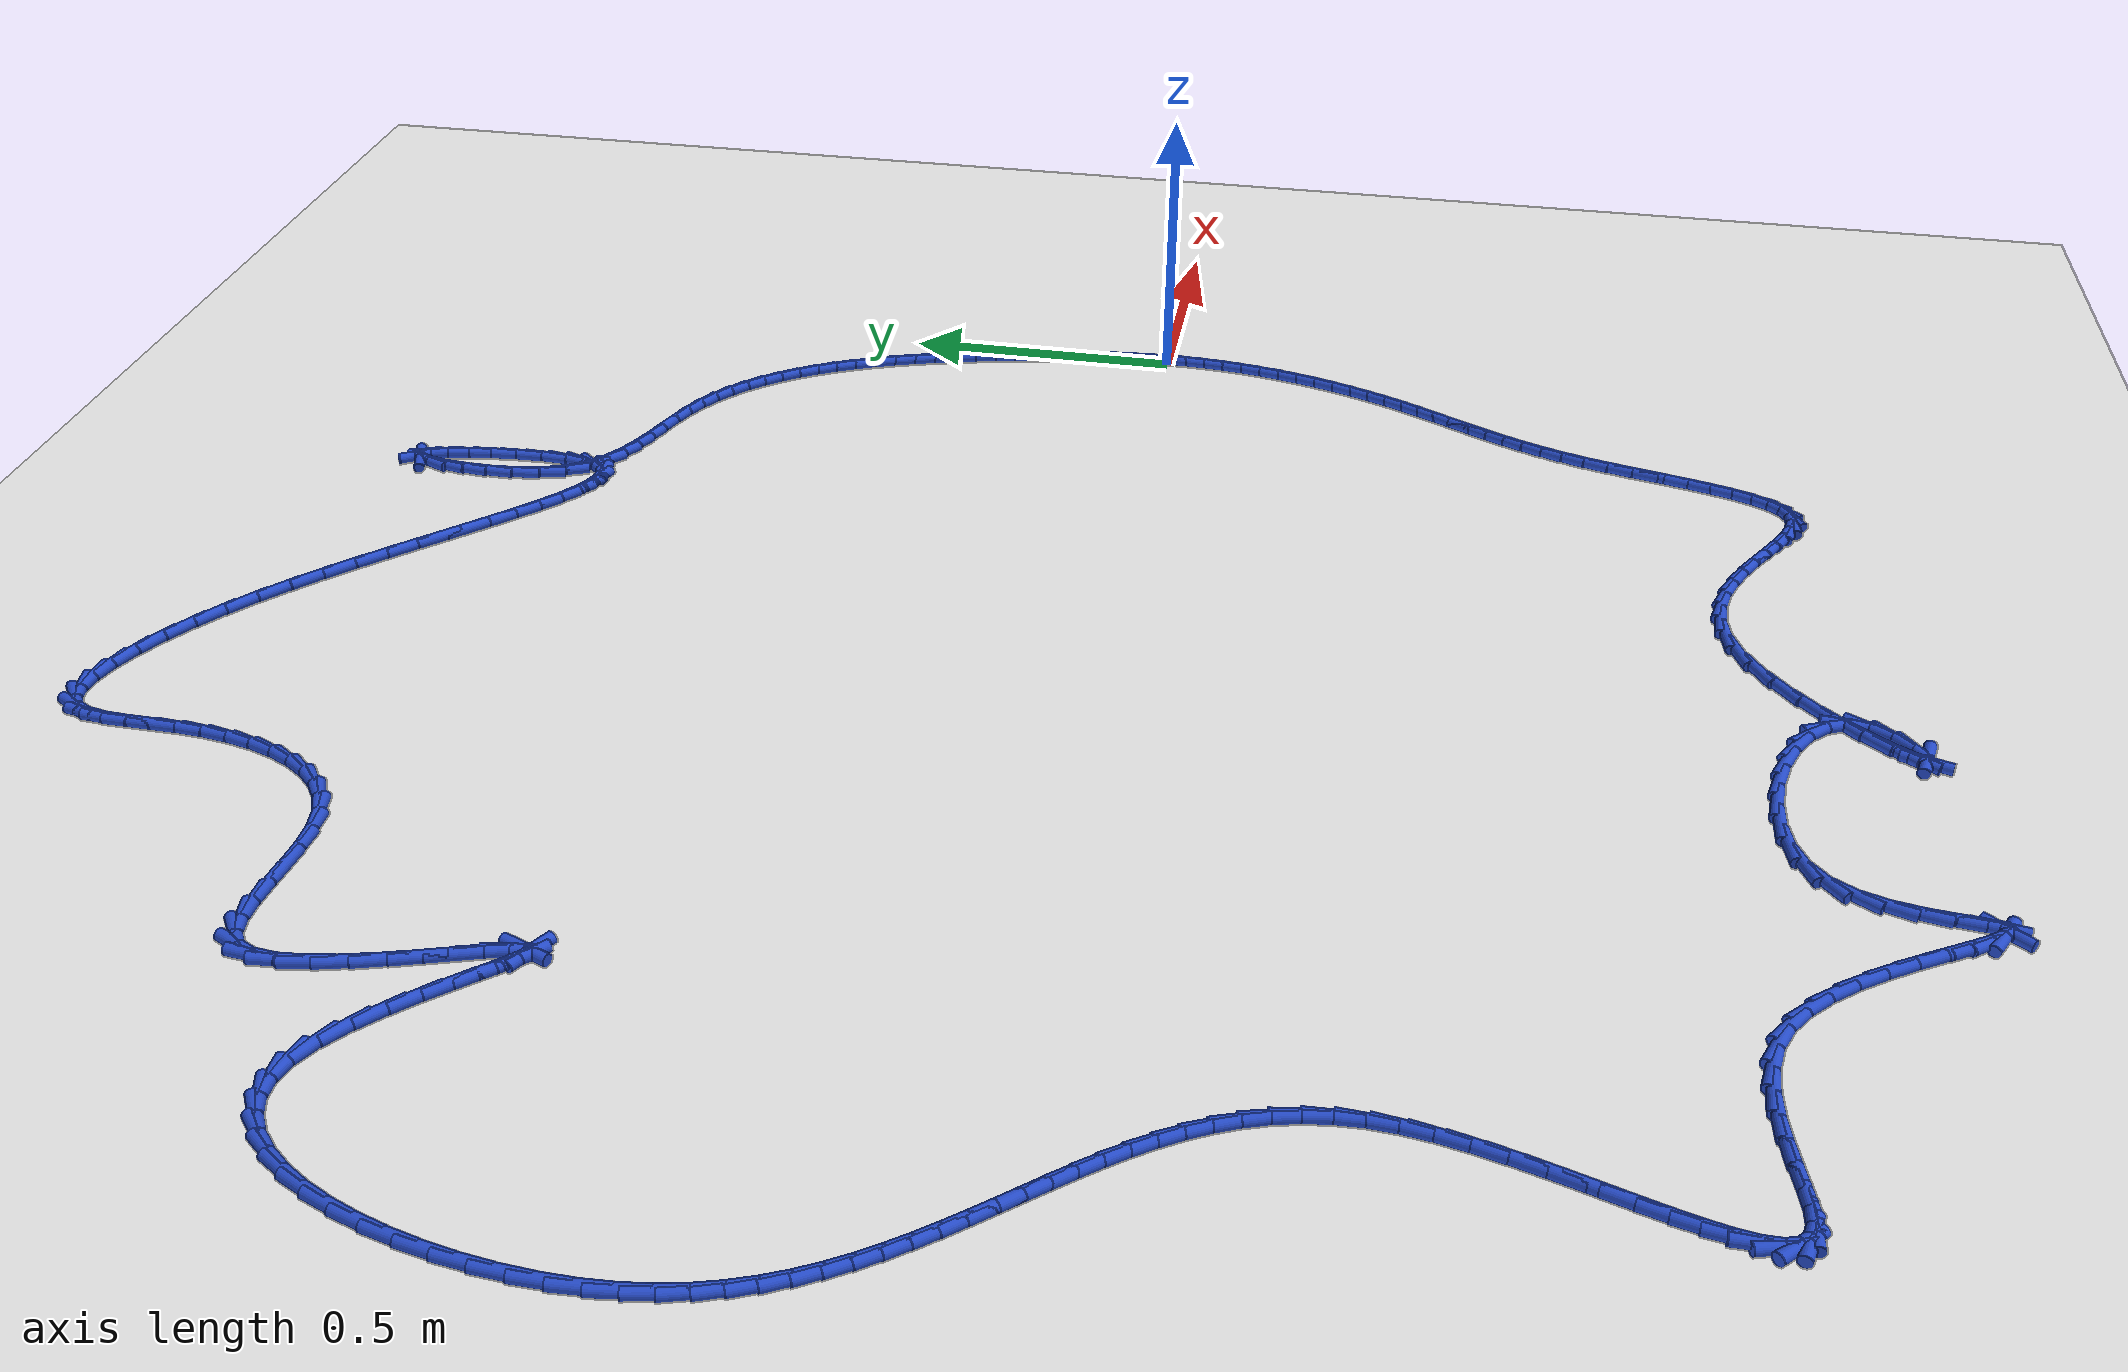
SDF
<sdf version="1.6">
 <world name="default">
  <light name="sun" type="directional">
   <pose>0 0 10 0 -0 0</pose>
   <diffuse>0.8 0.8 0.8 1</diffuse>
   <specular>0.2 0.2 0.2 1</specular>
   <attenuation>
    <range>1000</range>
    <constant>0.9</constant>
    <linear>0.01</linear>
    <quadratic>0.001</quadratic>
   </attenuation>
   <direction>-0.5 0.1 -0.9</direction>
  </light>
  <model name="ground_plane">
   <static>1</static>
   <link name="link">
    <collision name="collision">
     <geometry><plane><normal>0 0 1</normal><size>100 100</size></plane></geometry>
     <surface><friction><ode><mu>100</mu><mu2>50</mu2></ode></friction></surface>
    </collision>
    <visual name="visual">
     <cast_shadows>0</cast_shadows>
     <geometry><plane><normal>0 0 1</normal><size>100 100</size></plane></geometry>
     <material>
      <script><uri>file://media/materials/scripts/gazebo.material</uri><name>Gazebo/WhiteGlow</name></script>
     </material>
    </visual>
   </link>
  </model>
  <gravity>0 0 -9.8</gravity>
  <magnetic_field>6e-06 2.3e-05 -4.2e-05</magnetic_field>
  <atmosphere type="adiabatic"/>
  <physics name="default_physics" default="0" type="ode">
   <max_step_size>0.001</max_step_size>
   <real_time_factor>1</real_time_factor>
   <real_time_update_rate>1000</real_time_update_rate>
  </physics>
  <scene><ambient>0.4 0.4 0.4 1</ambient><background>0.7 0.7 0.7 1</background><shadows>1</shadows></scene>
  <spherical_coordinates>
   <surface_model>EARTH_WGS84</surface_model>
   <latitude_deg>0</latitude_deg>
   <longitude_deg>0</longitude_deg>
   <elevation>0</elevation>
   <heading_deg>0</heading_deg>
  </spherical_coordinates>
  <model name="line">
   <link name="link_0">
    <pose>1.9949319973733282e-17 2.7755575615628914e-17 0.01 0 1.57 -1.537967544123048</pose>
    <collision name="collision">
     <geometry><cylinder><radius>0.01</radius><length>0.08</length></cylinder></geometry>
    </collision>
    <visual name="visual">
     <material>
      <script><name>Gazebo/Blue</name><uri>file://media/materials/scripts/gazebo.material</uri></script>
     </material>
     <geometry><cylinder><radius>0.01</radius><length>0.08</length></cylinder></geometry>
    </visual>
   </link>
   <link name="link_1">
    <pose>-0.0012037588185470295 0.03665461365363052 0.01 0 1.57 -1.499386344822641</pose>
    <collision name="collision">
     <geometry><cylinder><radius>0.01</radius><length>0.08</length></cylinder></geometry>
    </collision>
    <visual name="visual">
     <material>
      <script><name>Gazebo/Blue</name><uri>file://media/materials/scripts/gazebo.material</uri></script>
     </material>
     <geometry><cylinder><radius>0.01</radius><length>0.08</length></cylinder></geometry>
    </visual>
   </link>
   <link name="link_2">
    <pose>-0.0038199700766872713 0.07322881028822745 0.01 0 1.57 -1.4655532369670923</pose>
    <collision name="collision">
     <geometry><cylinder><radius>0.01</radius><length>0.08</length></cylinder></geometry>
    </collision>
    <visual name="visual">
     <material>
      <script><name>Gazebo/Blue</name><uri>file://media/materials/scripts/gazebo.material</uri></script>
     </material>
     <geometry><cylinder><radius>0.01</radius><length>0.08</length></cylinder></geometry>
    </visual>
   </link>
   <link name="link_3">
    <pose>-0.007688108798061293 0.10984733663296763 0.01 0 1.57 -1.4367887436755327</pose>
    <collision name="collision">
     <geometry><cylinder><radius>0.01</radius><length>0.08</length></cylinder></geometry>
    </collision>
    <visual name="visual">
     <material>
      <script><name>Gazebo/Blue</name><uri>file://media/materials/scripts/gazebo.material</uri></script>
     </material>
     <geometry><cylinder><radius>0.01</radius><length>0.08</length></cylinder></geometry>
    </visual>
   </link>
   <link name="link_4">
    <pose>-0.012647650006309664 0.1466349394170278 0.01 0 1.57 -1.4132616604367338</pose>
    <collision name="collision">
     <geometry><cylinder><radius>0.01</radius><length>0.08</length></cylinder></geometry>
    </collision>
    <visual name="visual">
     <material>
      <script><name>Gazebo/Blue</name><uri>file://media/materials/scripts/gazebo.material</uri></script>
     </material>
     <geometry><cylinder><radius>0.01</radius><length>0.08</length></cylinder></geometry>
    </visual>
   </link>
   <link name="link_5">
    <pose>-0.018538068725072968 0.1837163653695848 0.01 0 1.57 -1.3950090810265992</pose>
    <collision name="collision">
     <geometry><cylinder><radius>0.01</radius><length>0.08</length></cylinder></geometry>
    </collision>
    <visual name="visual">
     <material>
      <script><name>Gazebo/Blue</name><uri>file://media/materials/scripts/gazebo.material</uri></script>
     </material>
     <geometry><cylinder><radius>0.01</radius><length>0.08</length></cylinder></geometry>
    </visual>
   </link>
   <link name="link_6">
    <pose>-0.025198839977991796 0.2212163612198155 0.01 0 1.57 -1.3814095369820483</pose>
    <collision name="collision">
     <geometry><cylinder><radius>0.01</radius><length>0.08</length></cylinder></geometry>
    </collision>
    <visual name="visual">
     <material>
      <script><name>Gazebo/Blue</name><uri>file://media/materials/scripts/gazebo.material</uri></script>
     </material>
     <geometry><cylinder><radius>0.01</radius><length>0.08</length></cylinder></geometry>
    </visual>
   </link>
   <link name="link_7">
    <pose>-0.03248705114378532 0.259238368000335 0.01 0 1.57 -1.3675903152002524</pose>
    <collision name="collision">
     <geometry><cylinder><radius>0.01</radius><length>0.08</length></cylinder></geometry>
    </collision>
    <visual name="visual">
     <material>
      <script><name>Gazebo/Blue</name><uri>file://media/materials/scripts/gazebo.material</uri></script>
     </material>
     <geometry><cylinder><radius>0.01</radius><length>0.08</length></cylinder></geometry>
    </visual>
   </link>
   <link name="link_8">
    <pose>-0.040412335389427054 0.29770129183847394 0.01 0 1.57 -1.3510456557534498</pose>
    <collision name="collision">
     <geometry><cylinder><radius>0.01</radius><length>0.08</length></cylinder></geometry>
    </collision>
    <visual name="visual">
     <material>
      <script><name>Gazebo/Blue</name><uri>file://media/materials/scripts/gazebo.material</uri></script>
     </material>
     <geometry><cylinder><radius>0.01</radius><length>0.08</length></cylinder></geometry>
    </visual>
   </link>
   <link name="link_9">
    <pose>-0.04906255524476291 0.3364294046652767 0.01 0 1.57 -1.3316585324085675</pose>
    <collision name="collision">
     <geometry><cylinder><radius>0.01</radius><length>0.08</length></cylinder></geometry>
    </collision>
    <visual name="visual">
     <material>
      <script><name>Gazebo/Blue</name><uri>file://media/materials/scripts/gazebo.material</uri></script>
     </material>
     <geometry><cylinder><radius>0.01</radius><length>0.08</length></cylinder></geometry>
    </visual>
   </link>
   <link name="link_10">
    <pose>-0.058526210407279185 0.3752462076289859 0.01 0 1.57 -1.309281534916501</pose>
    <collision name="collision">
     <geometry><cylinder><radius>0.01</radius><length>0.08</length></cylinder></geometry>
    </collision>
    <visual name="visual">
     <material>
      <script><name>Gazebo/Blue</name><uri>file://media/materials/scripts/gazebo.material</uri></script>
     </material>
     <geometry><cylinder><radius>0.01</radius><length>0.08</length></cylinder></geometry>
    </visual>
   </link>
   <link name="link_11">
    <pose>-0.0688918005744622 0.4139752018778441 0.01 0 1.57 -1.283719121978787</pose>
    <collision name="collision">
     <geometry><cylinder><radius>0.01</radius><length>0.08</length></cylinder></geometry>
    </collision>
    <visual name="visual">
     <material>
      <script><name>Gazebo/Blue</name><uri>file://media/materials/scripts/gazebo.material</uri></script>
     </material>
     <geometry><cylinder><radius>0.01</radius><length>0.08</length></cylinder></geometry>
    </visual>
   </link>
   <link name="link_12">
    <pose>-0.08024782544379819 0.45243988856009304 0.01 0 1.57 -1.2547292285573373</pose>
    <collision name="collision">
     <geometry><cylinder><radius>0.01</radius><length>0.08</length></cylinder></geometry>
    </collision>
    <visual name="visual">
     <material>
      <script><name>Gazebo/Blue</name><uri>file://media/materials/scripts/gazebo.material</uri></script>
     </material>
     <geometry><cylinder><radius>0.01</radius><length>0.08</length></cylinder></geometry>
    </visual>
   </link>
   <link name="link_13">
    <pose>-0.0926827847127735 0.4904637688239758 0.01 0 1.57 -1.222025265144609</pose>
    <collision name="collision">
     <geometry><cylinder><radius>0.01</radius><length>0.08</length></cylinder></geometry>
    </collision>
    <visual name="visual">
     <material>
      <script><name>Gazebo/Blue</name><uri>file://media/materials/scripts/gazebo.material</uri></script>
     </material>
     <geometry><cylinder><radius>0.01</radius><length>0.08</length></cylinder></geometry>
    </visual>
   </link>
   <link name="link_14">
    <pose>-0.10628517807887443 0.5278703438177345 0.01 0 1.57 -1.18527969218386</pose>
    <collision name="collision">
     <geometry><cylinder><radius>0.01</radius><length>0.08</length></cylinder></geometry>
    </collision>
    <visual name="visual">
     <material>
      <script><name>Gazebo/Blue</name><uri>file://media/materials/scripts/gazebo.material</uri></script>
     </material>
     <geometry><cylinder><radius>0.01</radius><length>0.08</length></cylinder></geometry>
    </visual>
   </link>
   <link name="link_15">
    <pose>-0.12114350523958722 0.5644831146896113 0.01 0 1.57 -1.1441307266807934</pose>
    <collision name="collision">
     <geometry><cylinder><radius>0.01</radius><length>0.08</length></cylinder></geometry>
    </collision>
    <visual name="visual">
     <material>
      <script><name>Gazebo/Blue</name><uri>file://media/materials/scripts/gazebo.material</uri></script>
     </material>
     <geometry><cylinder><radius>0.01</radius><length>0.08</length></cylinder></geometry>
    </visual>
   </link>
   <link name="link_16">
    <pose>-0.13734626589239818 0.6001255825878488 0.01 0 1.57 -1.0981942273242975</pose>
    <collision name="collision">
     <geometry><cylinder><radius>0.01</radius><length>0.08</length></cylinder></geometry>
    </collision>
    <visual name="visual">
     <material>
      <script><name>Gazebo/Blue</name><uri>file://media/materials/scripts/gazebo.material</uri></script>
     </material>
     <geometry><cylinder><radius>0.01</radius><length>0.08</length></cylinder></geometry>
    </visual>
   </link>
   <link name="link_17">
    <pose>-0.15498195973479367 0.6346212486606895 0.01 0 1.57 -1.0470833227121197</pose>
    <collision name="collision">
     <geometry><cylinder><radius>0.01</radius><length>0.08</length></cylinder></geometry>
    </collision>
    <visual name="visual">
     <material>
      <script><name>Gazebo/Blue</name><uri>file://media/materials/scripts/gazebo.material</uri></script>
     </material>
     <geometry><cylinder><radius>0.01</radius><length>0.08</length></cylinder></geometry>
    </visual>
   </link>
   <link name="link_18">
    <pose>-0.17413908646425988 0.6677936140563754 0.01 0 1.57 -0.9904386852999633</pose>
    <collision name="collision">
     <geometry><cylinder><radius>0.01</radius><length>0.08</length></cylinder></geometry>
    </collision>
    <visual name="visual">
     <material>
      <script><name>Gazebo/Blue</name><uri>file://media/materials/scripts/gazebo.material</uri></script>
     </material>
     <geometry><cylinder><radius>0.01</radius><length>0.08</length></cylinder></geometry>
    </visual>
   </link>
   <link name="link_19">
    <pose>-0.19490614577828325 0.6994661799231494 0.01 0 1.57 -0.9279721045907157</pose>
    <collision name="collision">
     <geometry><cylinder><radius>0.01</radius><length>0.08</length></cylinder></geometry>
    </collision>
    <visual name="visual">
     <material>
      <script><name>Gazebo/Blue</name><uri>file://media/materials/scripts/gazebo.material</uri></script>
     </material>
     <geometry><cylinder><radius>0.01</radius><length>0.08</length></cylinder></geometry>
    </visual>
   </link>
   <link name="link_20">
    <pose>-0.21737163737434995 0.7294624474092537 0.01 0 1.57 -0.8595245318368444</pose>
    <collision name="collision">
     <geometry><cylinder><radius>0.01</radius><length>0.08</length></cylinder></geometry>
    </collision>
    <visual name="visual">
     <material>
      <script><name>Gazebo/Blue</name><uri>file://media/materials/scripts/gazebo.material</uri></script>
     </material>
     <geometry><cylinder><radius>0.01</radius><length>0.08</length></cylinder></geometry>
    </visual>
   </link>
   <link name="link_21">
    <pose>-0.24162406094994635 0.7576059176629304 0.01 0 1.57 -0.7851362845432149</pose>
    <collision name="collision">
     <geometry><cylinder><radius>0.01</radius><length>0.08</length></cylinder></geometry>
    </collision>
    <visual name="visual">
     <material>
      <script><name>Gazebo/Blue</name><uri>file://media/materials/scripts/gazebo.material</uri></script>
     </material>
     <geometry><cylinder><radius>0.01</radius><length>0.08</length></cylinder></geometry>
    </visual>
   </link>
   <link name="link_22">
    <pose>-0.26775191620255867 0.7837200918324221 0.01 0 1.57 -0.7051211690797357</pose>
    <collision name="collision">
     <geometry><cylinder><radius>0.01</radius><length>0.08</length></cylinder></geometry>
    </collision>
    <visual name="visual">
     <material>
      <script><name>Gazebo/Blue</name><uri>file://media/materials/scripts/gazebo.material</uri></script>
     </material>
     <geometry><cylinder><radius>0.01</radius><length>0.08</length></cylinder></geometry>
    </visual>
   </link>
   <link name="link_23">
    <pose>-0.29584370282967326 0.8076284710659711 0.01 0 1.57 -0.6201286901621793</pose>
    <collision name="collision">
     <geometry><cylinder><radius>0.01</radius><length>0.08</length></cylinder></geometry>
    </collision>
    <visual name="visual">
     <material>
      <script><name>Gazebo/Blue</name><uri>file://media/materials/scripts/gazebo.material</uri></script>
     </material>
     <geometry><cylinder><radius>0.01</radius><length>0.08</length></cylinder></geometry>
    </visual>
   </link>
   <link name="link_24">
    <pose>-0.3259879205287765 0.8291545565118202 0.01 0 1.57 -0.5311722789709444</pose>
    <collision name="collision">
     <geometry><cylinder><radius>0.01</radius><length>0.08</length></cylinder></geometry>
    </collision>
    <visual name="visual">
     <material>
      <script><name>Gazebo/Blue</name><uri>file://media/materials/scripts/gazebo.material</uri></script>
     </material>
     <geometry><cylinder><radius>0.01</radius><length>0.08</length></cylinder></geometry>
    </visual>
   </link>
   <link name="link_25">
    <pose>-0.35827306899735456 0.8481218493182112 0.01 0 1.57 -0.4399042992422587</pose>
    <collision name="collision">
     <geometry><cylinder><radius>0.01</radius><length>0.08</length></cylinder></geometry>
    </collision>
    <visual name="visual">
     <material>
      <script><name>Gazebo/Blue</name><uri>file://media/materials/scripts/gazebo.material</uri></script>
     </material>
     <geometry><cylinder><radius>0.01</radius><length>0.08</length></cylinder></geometry>
    </visual>
   </link>
   <link name="link_26">
    <pose>-0.39278040297476985 0.864363196086521 0.01 0 1.57 -0.36426872050714515</pose>
    <collision name="collision">
     <geometry><cylinder><radius>0.01</radius><length>0.08</length></cylinder></geometry>
    </collision>
    <visual name="visual">
     <material>
      <script><name>Gazebo/Blue</name><uri>file://media/materials/scripts/gazebo.material</uri></script>
     </material>
     <geometry><cylinder><radius>0.01</radius><length>0.08</length></cylinder></geometry>
    </visual>
   </link>
   <link name="link_27">
    <pose>-0.42918002552633405 0.8782417982711164 0.01 0 1.57 -0.32747956733553923</pose>
    <collision name="collision">
     <geometry><cylinder><radius>0.01</radius><length>0.08</length></cylinder></geometry>
    </collision>
    <visual name="visual">
     <material>
      <script><name>Gazebo/Blue</name><uri>file://media/materials/scripts/gazebo.material</uri></script>
     </material>
     <geometry><cylinder><radius>0.01</radius><length>0.08</length></cylinder></geometry>
    </visual>
   </link>
   <link name="link_28">
    <pose>-0.46651793691202825 0.8909259031828297 0.01 0 1.57 -0.3290210018537713</pose>
    <collision name="collision">
     <geometry><cylinder><radius>0.01</radius><length>0.08</length></cylinder></geometry>
    </collision>
    <visual name="visual">
     <material>
      <script><name>Gazebo/Blue</name><uri>file://media/materials/scripts/gazebo.material</uri></script>
     </material>
     <geometry><cylinder><radius>0.01</radius><length>0.08</length></cylinder></geometry>
    </visual>
   </link>
   <link name="link_29">
    <pose>-0.5037879628153368 0.903651059426867 0.01 0 1.57 -0.3691033247265653</pose>
    <collision name="collision">
     <geometry><cylinder><radius>0.01</radius><length>0.08</length></cylinder></geometry>
    </collision>
    <visual name="visual">
     <material>
      <script><name>Gazebo/Blue</name><uri>file://media/materials/scripts/gazebo.material</uri></script>
     </material>
     <geometry><cylinder><radius>0.01</radius><length>0.08</length></cylinder></geometry>
    </visual>
   </link>
   <link name="link_30">
    <pose>-0.5399839289197447 0.9176528156084339 0.01 0 1.57 -0.4508107684889604</pose>
    <collision name="collision">
     <geometry><cylinder><radius>0.01</radius><length>0.08</length></cylinder></geometry>
    </collision>
    <visual name="visual">
     <material>
      <script><name>Gazebo/Blue</name><uri>file://media/materials/scripts/gazebo.material</uri></script>
     </material>
     <geometry><cylinder><radius>0.01</radius><length>0.08</length></cylinder></geometry>
    </visual>
   </link>
   <link name="link_31">
    <pose>-0.574099660908736 0.9341667203327363 0.01 0 1.57 -0.5784689480780759</pose>
    <collision name="collision">
     <geometry><cylinder><radius>0.01</radius><length>0.08</length></cylinder></geometry>
    </collision>
    <visual name="visual">
     <material>
      <script><name>Gazebo/Blue</name><uri>file://media/materials/scripts/gazebo.material</uri></script>
     </material>
     <geometry><cylinder><radius>0.01</radius><length>0.08</length></cylinder></geometry>
    </visual>
   </link>
   <link name="link_32">
    <pose>-0.6051289844657957 0.9544283222049803 0.01 0 1.57 -0.7529863351477291</pose>
    <collision name="collision">
     <geometry><cylinder><radius>0.01</radius><length>0.08</length></cylinder></geometry>
    </collision>
    <visual name="visual">
     <material>
      <script><name>Gazebo/Blue</name><uri>file://media/materials/scripts/gazebo.material</uri></script>
     </material>
     <geometry><cylinder><radius>0.01</radius><length>0.08</length></cylinder></geometry>
    </visual>
   </link>
   <link name="link_33">
    <pose>-0.632065725274408 0.9796731698303713 0.01 0 1.57 -0.9640610305196036</pose>
    <collision name="collision">
     <geometry><cylinder><radius>0.01</radius><length>0.08</length></cylinder></geometry>
    </collision>
    <visual name="visual">
     <material>
      <script><name>Gazebo/Blue</name><uri>file://media/materials/scripts/gazebo.material</uri></script>
     </material>
     <geometry><cylinder><radius>0.01</radius><length>0.08</length></cylinder></geometry>
    </visual>
   </link>
   <link name="link_34">
    <pose>-0.6539037090180577 1.0111368118141157 0.01 0 1.57 -1.1863665383951332</pose>
    <collision name="collision">
     <geometry><cylinder><radius>0.01</radius><length>0.08</length></cylinder></geometry>
    </collision>
    <visual name="visual">
     <material>
      <script><name>Gazebo/Blue</name><uri>file://media/materials/scripts/gazebo.material</uri></script>
     </material>
     <geometry><cylinder><radius>0.01</radius><length>0.08</length></cylinder></geometry>
    </visual>
   </link>
   <link name="link_35">
    <pose>-0.6696422845561799 1.050039917272067 0.01 0 1.57 -1.3712676362038603</pose>
    <collision name="collision">
     <geometry><cylinder><radius>0.01</radius><length>0.08</length></cylinder></geometry>
    </collision>
    <visual name="visual">
     <material>
      <script><name>Gazebo/Blue</name><uri>file://media/materials/scripts/gazebo.material</uri></script>
     </material>
     <geometry><cylinder><radius>0.01</radius><length>0.08</length></cylinder></geometry>
    </visual>
   </link>
   <link name="link_36">
    <pose>-0.6789149964960828 1.0958946258504128 0.01 0 1.57 -1.4964327469059333</pose>
    <collision name="collision">
     <geometry><cylinder><radius>0.01</radius><length>0.08</length></cylinder></geometry>
    </collision>
    <visual name="visual">
     <material>
      <script><name>Gazebo/Blue</name><uri>file://media/materials/scripts/gazebo.material</uri></script>
     </material>
     <geometry><cylinder><radius>0.01</radius><length>0.08</length></cylinder></geometry>
    </visual>
   </link>
   <link name="link_37">
    <pose>-0.6825691599199596 1.1449431678137225 0.01 0 1.57 1.5504297283499393</pose>
    <collision name="collision">
     <geometry><cylinder><radius>0.01</radius><length>0.08</length></cylinder></geometry>
    </collision>
    <visual name="visual">
     <material>
      <script><name>Gazebo/Blue</name><uri>file://media/materials/scripts/gazebo.material</uri></script>
     </material>
     <geometry><cylinder><radius>0.01</radius><length>0.08</length></cylinder></geometry>
    </visual>
   </link>
   <link name="link_38">
    <pose>-0.6815890739234766 1.1930587371713155 0.01 0 1.57 1.4636722464115142</pose>
    <collision name="collision">
     <geometry><cylinder><radius>0.01</radius><length>0.08</length></cylinder></geometry>
    </collision>
    <visual name="visual">
     <material>
      <script><name>Gazebo/Blue</name><uri>file://media/materials/scripts/gazebo.material</uri></script>
     </material>
     <geometry><cylinder><radius>0.01</radius><length>0.08</length></cylinder></geometry>
    </visual>
   </link>
   <link name="link_39">
    <pose>-0.6769590376022994 1.2361145279325125 0.01 0 1.57 1.3586305198370214</pose>
    <collision name="collision">
     <geometry><cylinder><radius>0.01</radius><length>0.08</length></cylinder></geometry>
    </collision>
    <visual name="visual">
     <material>
      <script><name>Gazebo/Blue</name><uri>file://media/materials/scripts/gazebo.material</uri></script>
     </material>
     <geometry><cylinder><radius>0.01</radius><length>0.08</length></cylinder></geometry>
    </visual>
   </link>
   <link name="link_40">
    <pose>-0.6696633500520935 1.269983734106632 0.01 0 1.57 1.1590446876044256</pose>
    <collision name="collision">
     <geometry><cylinder><radius>0.01</radius><length>0.08</length></cylinder></geometry>
    </collision>
    <visual name="visual">
     <material>
      <script><name>Gazebo/Blue</name><uri>file://media/materials/scripts/gazebo.material</uri></script>
     </material>
     <geometry><cylinder><radius>0.01</radius><length>0.08</length></cylinder></geometry>
    </visual>
   </link>
   <link name="link_41">
    <pose>-0.6606863103685253 1.2905395497029946 0.01 0 1.57 0.3180422039211436</pose>
    <collision name="collision">
     <geometry><cylinder><radius>0.01</radius><length>0.08</length></cylinder></geometry>
    </collision>
    <visual name="visual">
     <material>
      <script><name>Gazebo/Blue</name><uri>file://media/materials/scripts/gazebo.material</uri></script>
     </material>
     <geometry><cylinder><radius>0.01</radius><length>0.08</length></cylinder></geometry>
    </visual>
   </link>
   <link name="link_42">
    <pose>-0.65100818478211 1.2937257629691132 0.01 0 1.57 -1.0026407274218863</pose>
    <collision name="collision">
     <geometry><cylinder><radius>0.01</radius><length>0.08</length></cylinder></geometry>
    </collision>
    <visual name="visual">
     <material>
      <script><name>Gazebo/Blue</name><uri>file://media/materials/scripts/gazebo.material</uri></script>
     </material>
     <geometry><cylinder><radius>0.01</radius><length>0.08</length></cylinder></geometry>
    </visual>
   </link>
   <link name="link_43">
    <pose>-0.6414248655405949 1.2787135799741332 0.01 0 1.57 -1.276661519445988</pose>
    <collision name="collision">
     <geometry><cylinder><radius>0.01</radius><length>0.08</length></cylinder></geometry>
    </collision>
    <visual name="visual">
     <material>
      <script><name>Gazebo/Blue</name><uri>file://media/materials/scripts/gazebo.material</uri></script>
     </material>
     <geometry><cylinder><radius>0.01</radius><length>0.08</length></cylinder></geometry>
    </visual>
   </link>
   <link name="link_44">
    <pose>-0.6324754232459395 1.2491698017954371 0.01 0 1.57 -1.3786751088811442</pose>
    <collision name="collision">
     <geometry><cylinder><radius>0.01</radius><length>0.08</length></cylinder></geometry>
    </collision>
    <visual name="visual">
     <material>
      <script><name>Gazebo/Blue</name><uri>file://media/materials/scripts/gazebo.material</uri></script>
     </material>
     <geometry><cylinder><radius>0.01</radius><length>0.08</length></cylinder></geometry>
    </visual>
   </link>
   <link name="link_45">
    <pose>-0.6246799053636082 1.2090942244852467 0.01 0 1.57 -1.4402015747502128</pose>
    <collision name="collision">
     <geometry><cylinder><radius>0.01</radius><length>0.08</length></cylinder></geometry>
    </collision>
    <visual name="visual">
     <material>
      <script><name>Gazebo/Blue</name><uri>file://media/materials/scripts/gazebo.material</uri></script>
     </material>
     <geometry><cylinder><radius>0.01</radius><length>0.08</length></cylinder></geometry>
    </visual>
   </link>
   <link name="link_46">
    <pose>-0.6185583593590643 1.162486644095784 0.01 0 1.57 -1.4910402750979965</pose>
    <collision name="collision">
     <geometry><cylinder><radius>0.01</radius><length>0.08</length></cylinder></geometry>
    </collision>
    <visual name="visual">
     <material>
      <script><name>Gazebo/Blue</name><uri>file://media/materials/scripts/gazebo.material</uri></script>
     </material>
     <geometry><cylinder><radius>0.01</radius><length>0.08</length></cylinder></geometry>
    </visual>
   </link>
   <link name="link_47">
    <pose>-0.6146308326977716 1.113346856679269 0.01 0 1.57 -1.545347576350458</pose>
    <collision name="collision">
     <geometry><cylinder><radius>0.01</radius><length>0.08</length></cylinder></geometry>
    </collision>
    <visual name="visual">
     <material>
      <script><name>Gazebo/Blue</name><uri>file://media/materials/scripts/gazebo.material</uri></script>
     </material>
     <geometry><cylinder><radius>0.01</radius><length>0.08</length></cylinder></geometry>
    </visual>
   </link>
   <link name="link_48">
    <pose>-0.6134173728451937 1.0656746582879242 0.01 0 1.57 1.5229555133597268</pose>
    <collision name="collision">
     <geometry><cylinder><radius>0.01</radius><length>0.08</length></cylinder></geometry>
    </collision>
    <visual name="visual">
     <material>
      <script><name>Gazebo/Blue</name><uri>file://media/materials/scripts/gazebo.material</uri></script>
     </material>
     <geometry><cylinder><radius>0.01</radius><length>0.08</length></cylinder></geometry>
    </visual>
   </link>
   <link name="link_49">
    <pose>-0.6154380272667944 1.0234698449739708 0.01 0 1.57 1.400284303048932</pose>
    <collision name="collision">
     <geometry><cylinder><radius>0.01</radius><length>0.08</length></cylinder></geometry>
    </collision>
    <visual name="visual">
     <material>
      <script><name>Gazebo/Blue</name><uri>file://media/materials/scripts/gazebo.material</uri></script>
     </material>
     <geometry><cylinder><radius>0.01</radius><length>0.08</length></cylinder></geometry>
    </visual>
   </link>
   <link name="link_50">
    <pose>-0.6211488049852194 0.990303125683209 0.01 0 1.57 1.190419656338284</pose>
    <collision name="collision">
     <geometry><cylinder><radius>0.01</radius><length>0.08</length></cylinder></geometry>
    </collision>
    <visual name="visual">
     <material>
      <script><name>Gazebo/Blue</name><uri>file://media/materials/scripts/gazebo.material</uri></script>
     </material>
     <geometry><cylinder><radius>0.01</radius><length>0.08</length></cylinder></geometry>
    </visual>
   </link>
   <link name="link_51">
    <pose>-0.6305608229323674 0.9667642271343905 0.01 0 1.57 0.8453109891184138</pose>
    <collision name="collision">
     <geometry><cylinder><radius>0.01</radius><length>0.08</length></cylinder></geometry>
    </collision>
    <visual name="visual">
     <material>
      <script><name>Gazebo/Blue</name><uri>file://media/materials/scripts/gazebo.material</uri></script>
     </material>
     <geometry><cylinder><radius>0.01</radius><length>0.08</length></cylinder></geometry>
    </visual>
   </link>
   <link name="link_52">
    <pose>-0.6434963882672983 0.9521777634743991 0.01 0 1.57 0.36996330935486665</pose>
    <collision name="collision">
     <geometry><cylinder><radius>0.01</radius><length>0.08</length></cylinder></geometry>
    </collision>
    <visual name="visual">
     <material>
      <script><name>Gazebo/Blue</name><uri>file://media/materials/scripts/gazebo.material</uri></script>
     </material>
     <geometry><cylinder><radius>0.01</radius><length>0.08</length></cylinder></geometry>
    </visual>
   </link>
   <link name="link_53">
    <pose>-0.659777122350564 0.9458637536837778 0.01 0 1.57 -0.0656446612627032</pose>
    <collision name="collision">
     <geometry><cylinder><radius>0.01</radius><length>0.08</length></cylinder></geometry>
    </collision>
    <visual name="visual">
     <material>
      <script><name>Gazebo/Blue</name><uri>file://media/materials/scripts/gazebo.material</uri></script>
     </material>
     <geometry><cylinder><radius>0.01</radius><length>0.08</length></cylinder></geometry>
    </visual>
   </link>
   <link name="link_54">
    <pose>-0.6792246465427171 0.9471422167430713 0.01 0 1.57 -0.35004715925948304</pose>
    <collision name="collision">
     <geometry><cylinder><radius>0.01</radius><length>0.08</length></cylinder></geometry>
    </collision>
    <visual name="visual">
     <material>
      <script><name>Gazebo/Blue</name><uri>file://media/materials/scripts/gazebo.material</uri></script>
     </material>
     <geometry><cylinder><radius>0.01</radius><length>0.08</length></cylinder></geometry>
    </visual>
   </link>
   <link name="link_55">
    <pose>-0.70166058220431 0.9553331716328233 0.01 0 1.57 -0.5190624420955265</pose>
    <collision name="collision">
     <geometry><cylinder><radius>0.01</radius><length>0.08</length></cylinder></geometry>
    </collision>
    <visual name="visual">
     <material>
      <script><name>Gazebo/Blue</name><uri>file://media/materials/scripts/gazebo.material</uri></script>
     </material>
     <geometry><cylinder><radius>0.01</radius><length>0.08</length></cylinder></geometry>
    </visual>
   </link>
   <link name="link_56">
    <pose>-0.7269065506958953 0.9697566373335778 0.01 0 1.57 -0.6217539591754776</pose>
    <collision name="collision">
     <geometry><cylinder><radius>0.01</radius><length>0.08</length></cylinder></geometry>
    </collision>
    <visual name="visual">
     <material>
      <script><name>Gazebo/Blue</name><uri>file://media/materials/scripts/gazebo.material</uri></script>
     </material>
     <geometry><cylinder><radius>0.01</radius><length>0.08</length></cylinder></geometry>
    </visual>
   </link>
   <link name="link_57">
    <pose>-0.7547841733780253 0.9897326328258785 0.01 0 1.57 -0.6863681572205017</pose>
    <collision name="collision">
     <geometry><cylinder><radius>0.01</radius><length>0.08</length></cylinder></geometry>
    </collision>
    <visual name="visual">
     <material>
      <script><name>Gazebo/Blue</name><uri>file://media/materials/scripts/gazebo.material</uri></script>
     </material>
     <geometry><cylinder><radius>0.01</radius><length>0.08</length></cylinder></geometry>
    </visual>
   </link>
   <link name="link_58">
    <pose>-0.7851150716112525 1.0145811770902697 0.01 0 1.57 -0.7276382815180285</pose>
    <collision name="collision">
     <geometry><cylinder><radius>0.01</radius><length>0.08</length></cylinder></geometry>
    </collision>
    <visual name="visual">
     <material>
      <script><name>Gazebo/Blue</name><uri>file://media/materials/scripts/gazebo.material</uri></script>
     </material>
     <geometry><cylinder><radius>0.01</radius><length>0.08</length></cylinder></geometry>
    </visual>
   </link>
   <link name="link_59">
    <pose>-0.8177208667561294 1.0436222891072953 0.01 0 1.57 -0.753462220610442</pose>
    <collision name="collision">
     <geometry><cylinder><radius>0.01</radius><length>0.08</length></cylinder></geometry>
    </collision>
    <visual name="visual">
     <material>
      <script><name>Gazebo/Blue</name><uri>file://media/materials/scripts/gazebo.material</uri></script>
     </material>
     <geometry><cylinder><radius>0.01</radius><length>0.08</length></cylinder></geometry>
    </visual>
   </link>
   <link name="link_60">
    <pose>-0.8524231801732084 1.0761759878574988 0.01 0 1.57 -0.7682604973898399</pose>
    <collision name="collision">
     <geometry><cylinder><radius>0.01</radius><length>0.08</length></cylinder></geometry>
    </collision>
    <visual name="visual">
     <material>
      <script><name>Gazebo/Blue</name><uri>file://media/materials/scripts/gazebo.material</uri></script>
     </material>
     <geometry><cylinder><radius>0.01</radius><length>0.08</length></cylinder></geometry>
    </visual>
   </link>
   <link name="link_61">
    <pose>-0.889043633223042 1.1115622923214246 0.01 0 1.57 -0.7745778458253847</pose>
    <collision name="collision">
     <geometry><cylinder><radius>0.01</radius><length>0.08</length></cylinder></geometry>
    </collision>
    <visual name="visual">
     <material>
      <script><name>Gazebo/Blue</name><uri>file://media/materials/scripts/gazebo.material</uri></script>
     </material>
     <geometry><cylinder><radius>0.01</radius><length>0.08</length></cylinder></geometry>
    </visual>
   </link>
   <link name="link_62">
    <pose>-0.9274038472661822 1.1491012214796164 0.01 0 1.57 -0.7738696354495205</pose>
    <collision name="collision">
     <geometry><cylinder><radius>0.01</radius><length>0.08</length></cylinder></geometry>
    </collision>
    <visual name="visual">
     <material>
      <script><name>Gazebo/Blue</name><uri>file://media/materials/scripts/gazebo.material</uri></script>
     </material>
     <geometry><cylinder><radius>0.01</radius><length>0.08</length></cylinder></geometry>
    </visual>
   </link>
   <link name="link_63">
    <pose>-0.9673254436631822 1.1881127943126184 0.01 0 1.57 -0.7669021078882596</pose>
    <collision name="collision">
     <geometry><cylinder><radius>0.01</radius><length>0.08</length></cylinder></geometry>
    </collision>
    <visual name="visual">
     <material>
      <script><name>Gazebo/Blue</name><uri>file://media/materials/scripts/gazebo.material</uri></script>
     </material>
     <geometry><cylinder><radius>0.01</radius><length>0.08</length></cylinder></geometry>
    </visual>
   </link>
   <link name="link_64">
    <pose>-1.0086300437745939 1.2279170298009745 0.01 0 1.57 -0.7539584549950286</pose>
    <collision name="collision">
     <geometry><cylinder><radius>0.01</radius><length>0.08</length></cylinder></geometry>
    </collision>
    <visual name="visual">
     <material>
      <script><name>Gazebo/Blue</name><uri>file://media/materials/scripts/gazebo.material</uri></script>
     </material>
     <geometry><cylinder><radius>0.01</radius><length>0.08</length></cylinder></geometry>
    </visual>
   </link>
   <link name="link_65">
    <pose>-1.0511392689609704 1.2678339469252284 0.01 0 1.57 -0.7349391392507844</pose>
    <collision name="collision">
     <geometry><cylinder><radius>0.01</radius><length>0.08</length></cylinder></geometry>
    </collision>
    <visual name="visual">
     <material>
      <script><name>Gazebo/Blue</name><uri>file://media/materials/scripts/gazebo.material</uri></script>
     </material>
     <geometry><cylinder><radius>0.01</radius><length>0.08</length></cylinder></geometry>
    </visual>
   </link>
   <link name="link_66">
    <pose>-1.0946747405828632 1.3071835646659242 0.01 0 1.57 -0.709398248356987</pose>
    <collision name="collision">
     <geometry><cylinder><radius>0.01</radius><length>0.08</length></cylinder></geometry>
    </collision>
    <visual name="visual">
     <material>
      <script><name>Gazebo/Blue</name><uri>file://media/materials/scripts/gazebo.material</uri></script>
     </material>
     <geometry><cylinder><radius>0.01</radius><length>0.08</length></cylinder></geometry>
    </visual>
   </link>
   <link name="link_67">
    <pose>-1.139058080000825 1.3452859020036054 0.01 0 1.57 -0.6765358837936911</pose>
    <collision name="collision">
     <geometry><cylinder><radius>0.01</radius><length>0.08</length></cylinder></geometry>
    </collision>
    <visual name="visual">
     <material>
      <script><name>Gazebo/Blue</name><uri>file://media/materials/scripts/gazebo.material</uri></script>
     </material>
     <geometry><cylinder><radius>0.01</radius><length>0.08</length></cylinder></geometry>
    </visual>
   </link>
   <link name="link_68">
    <pose>-1.1841109085754091 1.3814609779188172 0.01 0 1.57 -0.6351568115690917</pose>
    <collision name="collision">
     <geometry><cylinder><radius>0.01</radius><length>0.08</length></cylinder></geometry>
    </collision>
    <visual name="visual">
     <material>
      <script><name>Gazebo/Blue</name><uri>file://media/materials/scripts/gazebo.material</uri></script>
     </material>
     <geometry><cylinder><radius>0.01</radius><length>0.08</length></cylinder></geometry>
    </visual>
   </link>
   <link name="link_69">
    <pose>-1.2296548476671676 1.4150288113921023 0.01 0 1.57 -0.5840671310520521</pose>
    <collision name="collision">
     <geometry><cylinder><radius>0.01</radius><length>0.08</length></cylinder></geometry>
    </collision>
    <visual name="visual">
     <material>
      <script><name>Gazebo/Blue</name><uri>file://media/materials/scripts/gazebo.material</uri></script>
     </material>
     <geometry><cylinder><radius>0.01</radius><length>0.08</length></cylinder></geometry>
    </visual>
   </link>
   <link name="link_70">
    <pose>-1.2754552670662003 1.4453027485287253 0.01 0 1.57 -0.5249370737210832</pose>
    <collision name="collision">
     <geometry><cylinder><radius>0.01</radius><length>0.08</length></cylinder></geometry>
    </collision>
    <visual name="visual">
     <material>
      <script><name>Gazebo/Blue</name><uri>file://media/materials/scripts/gazebo.material</uri></script>
     </material>
     <geometry><cylinder><radius>0.01</radius><length>0.08</length></cylinder></geometry>
    </visual>
   </link>
   <link name="link_71">
    <pose>-1.320747817566928 1.4715332972098294 0.01 0 1.57 -0.4551670922995273</pose>
    <collision name="collision">
     <geometry><cylinder><radius>0.01</radius><length>0.08</length></cylinder></geometry>
    </collision>
    <visual name="visual">
     <material>
      <script><name>Gazebo/Blue</name><uri>file://media/materials/scripts/gazebo.material</uri></script>
     </material>
     <geometry><cylinder><radius>0.01</radius><length>0.08</length></cylinder></geometry>
    </visual>
   </link>
   <link name="link_72">
    <pose>-1.3644774054517028 1.4929364755796188 0.01 0 1.57 -0.3667604441353496</pose>
    <collision name="collision">
     <geometry><cylinder><radius>0.01</radius><length>0.08</length></cylinder></geometry>
    </collision>
    <visual name="visual">
     <material>
      <script><name>Gazebo/Blue</name><uri>file://media/materials/scripts/gazebo.material</uri></script>
     </material>
     <geometry><cylinder><radius>0.01</radius><length>0.08</length></cylinder></geometry>
    </visual>
   </link>
   <link name="link_73">
    <pose>-1.4055859418133523 1.5087279464761993 0.01 0 1.57 -0.24593590143215077</pose>
    <collision name="collision">
     <geometry><cylinder><radius>0.01</radius><length>0.08</length></cylinder></geometry>
    </collision>
    <visual name="visual">
     <material>
      <script><name>Gazebo/Blue</name><uri>file://media/materials/scripts/gazebo.material</uri></script>
     </material>
     <geometry><cylinder><radius>0.01</radius><length>0.08</length></cylinder></geometry>
    </visual>
   </link>
   <link name="link_74">
    <pose>-1.4430153377447048 1.5181233727376748 0.01 0 1.57 -0.06765119833788105</pose>
    <collision name="collision">
     <geometry><cylinder><radius>0.01</radius><length>0.08</length></cylinder></geometry>
    </collision>
    <visual name="visual">
     <material>
      <script><name>Gazebo/Blue</name><uri>file://media/materials/scripts/gazebo.material</uri></script>
     </material>
     <geometry><cylinder><radius>0.01</radius><length>0.08</length></cylinder></geometry>
    </visual>
   </link>
   <link name="link_75">
    <pose>-1.475707504338588 1.5203384172021503 0.01 0 1.57 0.2105979048781416</pose>
    <collision name="collision">
     <geometry><cylinder><radius>0.01</radius><length>0.08</length></cylinder></geometry>
    </collision>
    <visual name="visual">
     <material>
      <script><name>Gazebo/Blue</name><uri>file://media/materials/scripts/gazebo.material</uri></script>
     </material>
     <geometry><cylinder><radius>0.01</radius><length>0.08</length></cylinder></geometry>
    </visual>
   </link>
   <link name="link_76">
    <pose>-1.5026043526878303 1.5145887427077307 0.01 0 1.57 0.6262358892823009</pose>
    <collision name="collision">
     <geometry><cylinder><radius>0.01</radius><length>0.08</length></cylinder></geometry>
    </collision>
    <visual name="visual">
     <material>
      <script><name>Gazebo/Blue</name><uri>file://media/materials/scripts/gazebo.material</uri></script>
     </material>
     <geometry><cylinder><radius>0.01</radius><length>0.08</length></cylinder></geometry>
    </visual>
   </link>
   <link name="link_77">
    <pose>-1.5226477938852603 1.5000900120925211 0.01 0 1.57 1.086765213088086</pose>
    <collision name="collision">
     <geometry><cylinder><radius>0.01</radius><length>0.08</length></cylinder></geometry>
    </collision>
    <visual name="visual">
     <material>
      <script><name>Gazebo/Blue</name><uri>file://media/materials/scripts/gazebo.material</uri></script>
     </material>
     <geometry><cylinder><radius>0.01</radius><length>0.08</length></cylinder></geometry>
    </visual>
   </link>
   <link name="link_78">
    <pose>-1.5351283942600615 1.476351141761856 0.01 0 1.57 1.3748497510444528</pose>
    <collision name="collision">
     <geometry><cylinder><radius>0.01</radius><length>0.08</length></cylinder></geometry>
    </collision>
    <visual name="visual">
     <material>
      <script><name>Gazebo/Blue</name><uri>file://media/materials/scripts/gazebo.material</uri></script>
     </material>
     <geometry><cylinder><radius>0.01</radius><length>0.08</length></cylinder></geometry>
    </visual>
   </link>
   <link name="link_79">
    <pose>-1.5414235827329585 1.4446363061395158 0.01 0 1.57 1.511036222267252</pose>
    <collision name="collision">
     <geometry><cylinder><radius>0.01</radius><length>0.08</length></cylinder></geometry>
    </collision>
    <visual name="visual">
     <material>
      <script><name>Gazebo/Blue</name><uri>file://media/materials/scripts/gazebo.material</uri></script>
     </material>
     <geometry><cylinder><radius>0.01</radius><length>0.08</length></cylinder></geometry>
    </visual>
   </link>
   <link name="link_80">
    <pose>-1.5436837984887584 1.406859857801822 0.01 0 1.57 1.5618052354049836</pose>
    <collision name="collision">
     <geometry><cylinder><radius>0.01</radius><length>0.08</length></cylinder></geometry>
    </collision>
    <visual name="visual">
     <material>
      <script><name>Gazebo/Blue</name><uri>file://media/materials/scripts/gazebo.material</uri></script>
     </material>
     <geometry><cylinder><radius>0.01</radius><length>0.08</length></cylinder></geometry>
    </visual>
   </link>
   <link name="link_81">
    <pose>-1.5440607390245298 1.3649372076902673 0.01 0 1.57 1.5561810024425535</pose>
    <collision name="collision">
     <geometry><cylinder><radius>0.01</radius><length>0.08</length></cylinder></geometry>
    </collision>
    <visual name="visual">
     <material>
      <script><name>Gazebo/Blue</name><uri>file://media/materials/scripts/gazebo.material</uri></script>
     </material>
     <geometry><cylinder><radius>0.01</radius><length>0.08</length></cylinder></geometry>
    </visual>
   </link>
   <link name="link_82">
    <pose>-1.5447061018373416 1.3207837667463456 0.01 0 1.57 1.5035635104177802</pose>
    <collision name="collision">
     <geometry><cylinder><radius>0.01</radius><length>0.08</length></cylinder></geometry>
    </collision>
    <visual name="visual">
     <material>
      <script><name>Gazebo/Blue</name><uri>file://media/materials/scripts/gazebo.material</uri></script>
     </material>
     <geometry><cylinder><radius>0.01</radius><length>0.08</length></cylinder></geometry>
    </visual>
   </link>
   <link name="link_83">
    <pose>-1.5477029546044057 1.2762766933040954 0.01 0 1.57 1.4257963768736024</pose>
    <collision name="collision">
     <geometry><cylinder><radius>0.01</radius><length>0.08</length></cylinder></geometry>
    </collision>
    <visual name="visual">
     <material>
      <script><name>Gazebo/Blue</name><uri>file://media/materials/scripts/gazebo.material</uri></script>
     </material>
     <geometry><cylinder><radius>0.01</radius><length>0.08</length></cylinder></geometry>
    </visual>
   </link>
   <link name="link_84">
    <pose>-1.5540665294275007 1.2326979598850527 0.01 0 1.57 1.338399476243084</pose>
    <collision name="collision">
     <geometry><cylinder><radius>0.01</radius><length>0.08</length></cylinder></geometry>
    </collision>
    <visual name="visual">
     <material>
      <script><name>Gazebo/Blue</name><uri>file://media/materials/scripts/gazebo.material</uri></script>
     </material>
     <geometry><cylinder><radius>0.01</radius><length>0.08</length></cylinder></geometry>
    </visual>
   </link>
   <link name="link_85">
    <pose>-1.5639685866569586 1.1908594081860662 0.01 0 1.57 1.2378767355041662</pose>
    <collision name="collision">
     <geometry><cylinder><radius>0.01</radius><length>0.08</length></cylinder></geometry>
    </collision>
    <visual name="visual">
     <material>
      <script><name>Gazebo/Blue</name><uri>file://media/materials/scripts/gazebo.material</uri></script>
     </material>
     <geometry><cylinder><radius>0.01</radius><length>0.08</length></cylinder></geometry>
    </visual>
   </link>
   <link name="link_86">
    <pose>-1.577557913581847 1.1515600752733384 0.01 0 1.57 1.1195749369986085</pose>
    <collision name="collision">
     <geometry><cylinder><radius>0.01</radius><length>0.08</length></cylinder></geometry>
    </collision>
    <visual name="visual">
     <material>
      <script><name>Gazebo/Blue</name><uri>file://media/materials/scripts/gazebo.material</uri></script>
     </material>
     <geometry><cylinder><radius>0.01</radius><length>0.08</length></cylinder></geometry>
    </visual>
   </link>
   <link name="link_87">
    <pose>-1.5949832974912341 1.1155989982130734 0.01 0 1.57 0.9785771842130928</pose>
    <collision name="collision">
     <geometry><cylinder><radius>0.01</radius><length>0.08</length></cylinder></geometry>
    </collision>
    <visual name="visual">
     <material>
      <script><name>Gazebo/Blue</name><uri>file://media/materials/scripts/gazebo.material</uri></script>
     </material>
     <geometry><cylinder><radius>0.01</radius><length>0.08</length></cylinder></geometry>
    </visual>
   </link>
   <link name="link_88">
    <pose>-1.6163935256741888 1.0837752140714743 0.01 0 1.57 0.8110183571782229</pose>
    <collision name="collision">
     <geometry><cylinder><radius>0.01</radius><length>0.08</length></cylinder></geometry>
    </collision>
    <visual name="visual">
     <material>
      <script><name>Gazebo/Blue</name><uri>file://media/materials/scripts/gazebo.material</uri></script>
     </material>
     <geometry><cylinder><radius>0.01</radius><length>0.08</length></cylinder></geometry>
    </visual>
   </link>
   <link name="link_89">
    <pose>-1.6419373854197787 1.0568877599147437 0.01 0 1.57 0.6168579800295301</pose>
    <collision name="collision">
     <geometry><cylinder><radius>0.01</radius><length>0.08</length></cylinder></geometry>
    </collision>
    <visual name="visual">
     <material>
      <script><name>Gazebo/Blue</name><uri>file://media/materials/scripts/gazebo.material</uri></script>
     </material>
     <geometry><cylinder><radius>0.01</radius><length>0.08</length></cylinder></geometry>
    </visual>
   </link>
   <link name="link_90">
    <pose>-1.6717636640170732 1.035735672809086 0.01 0 1.57 0.40331003302145924</pose>
    <collision name="collision">
     <geometry><cylinder><radius>0.01</radius><length>0.08</length></cylinder></geometry>
    </collision>
    <visual name="visual">
     <material>
      <script><name>Gazebo/Blue</name><uri>file://media/materials/scripts/gazebo.material</uri></script>
     </material>
     <geometry><cylinder><radius>0.01</radius><length>0.08</length></cylinder></geometry>
    </visual>
   </link>
   <link name="link_91">
    <pose>-1.7060211487551393 1.0211179898207037 0.01 0 1.57 0.18758997035802177</pose>
    <collision name="collision">
     <geometry><cylinder><radius>0.01</radius><length>0.08</length></cylinder></geometry>
    </collision>
    <visual name="visual">
     <material>
      <script><name>Gazebo/Blue</name><uri>file://media/materials/scripts/gazebo.material</uri></script>
     </material>
     <geometry><cylinder><radius>0.01</radius><length>0.08</length></cylinder></geometry>
    </visual>
   </link>
   <link name="link_92">
    <pose>-1.7448080892110236 1.013755382139723 0.01 0 1.57 0.023890533417448446</pose>
    <collision name="collision">
     <geometry><cylinder><radius>0.01</radius><length>0.08</length></cylinder></geometry>
    </collision>
    <visual name="visual">
     <material>
      <script><name>Gazebo/Blue</name><uri>file://media/materials/scripts/gazebo.material</uri></script>
     </material>
     <geometry><cylinder><radius>0.01</radius><length>0.08</length></cylinder></geometry>
    </visual>
   </link>
   <link name="link_93">
    <pose>-1.7871744676773487 1.0127430341501027 0.01 0 1.57 -0.06580806566914908</pose>
    <collision name="collision">
     <geometry><cylinder><radius>0.01</radius><length>0.08</length></cylinder></geometry>
    </collision>
    <visual name="visual">
     <material>
      <script><name>Gazebo/Blue</name><uri>file://media/materials/scripts/gazebo.material</uri></script>
     </material>
     <geometry><cylinder><radius>0.01</radius><length>0.08</length></cylinder></geometry>
    </visual>
   </link>
   <link name="link_94">
    <pose>-1.8311817234555605 1.015643254400255 0.01 0 1.57 -0.09849352963090716</pose>
    <collision name="collision">
     <geometry><cylinder><radius>0.01</radius><length>0.08</length></cylinder></geometry>
    </collision>
    <visual name="visual">
     <material>
      <script><name>Gazebo/Blue</name><uri>file://media/materials/scripts/gazebo.material</uri></script>
     </material>
     <geometry><cylinder><radius>0.01</radius><length>0.08</length></cylinder></geometry>
    </visual>
   </link>
   <link name="link_95">
    <pose>-1.8748527158807309 1.0199585277397525 0.01 0 1.57 -0.07800868328403475</pose>
    <collision name="collision">
     <geometry><cylinder><radius>0.01</radius><length>0.08</length></cylinder></geometry>
    </collision>
    <visual name="visual">
     <material>
      <script><name>Gazebo/Blue</name><uri>file://media/materials/scripts/gazebo.material</uri></script>
     </material>
     <geometry><cylinder><radius>0.01</radius><length>0.08</length></cylinder></geometry>
    </visual>
   </link>
   <link name="link_96">
    <pose>-1.916210304287928 1.0231913390181666 0.01 0 1.57 0.009365618285870675</pose>
    <collision name="collision">
     <geometry><cylinder><radius>0.01</radius><length>0.08</length></cylinder></geometry>
    </collision>
    <visual name="visual">
     <material>
      <script><name>Gazebo/Blue</name><uri>file://media/materials/scripts/gazebo.material</uri></script>
     </material>
     <geometry><cylinder><radius>0.01</radius><length>0.08</length></cylinder></geometry>
    </visual>
   </link>
   <link name="link_97">
    <pose>-1.9532773480122219 1.022844173085069 0.01 0 1.57 0.205648215844765</pose>
    <collision name="collision">
     <geometry><cylinder><radius>0.01</radius><length>0.08</length></cylinder></geometry>
    </collision>
    <visual name="visual">
     <material>
      <script><name>Gazebo/Blue</name><uri>file://media/materials/scripts/gazebo.material</uri></script>
     </material>
     <geometry><cylinder><radius>0.01</radius><length>0.08</length></cylinder></geometry>
    </visual>
   </link>
   <link name="link_98">
    <pose>-1.9840767063886828 1.0164195147900317 0.01 0 1.57 0.5868755918959616</pose>
    <collision name="collision">
     <geometry><cylinder><radius>0.01</radius><length>0.08</length></cylinder></geometry>
    </collision>
    <visual name="visual">
     <material>
      <script><name>Gazebo/Blue</name><uri>file://media/materials/scripts/gazebo.material</uri></script>
     </material>
     <geometry><cylinder><radius>0.01</radius><length>0.08</length></cylinder></geometry>
    </visual>
   </link>
   <link name="link_99">
    <pose>-2.0066312387523815 1.0014198489826267 0.01 0 1.57 1.1113923010783622</pose>
    <collision name="collision">
     <geometry><cylinder><radius>0.01</radius><length>0.08</length></cylinder></geometry>
    </collision>
    <visual name="visual">
     <material>
      <script><name>Gazebo/Blue</name><uri>file://media/materials/scripts/gazebo.material</uri></script>
     </material>
     <geometry><cylinder><radius>0.01</radius><length>0.08</length></cylinder></geometry>
    </visual>
   </link>
   <link name="link_100">
    <pose>-2.0193057757171697 0.9757995441773206 0.01 0 1.57 1.4694840434929044</pose>
    <collision name="collision">
     <geometry><cylinder><radius>0.01</radius><length>0.08</length></cylinder></geometry>
    </collision>
    <visual name="visual">
     <material>
      <script><name>Gazebo/Blue</name><uri>file://media/materials/scripts/gazebo.material</uri></script>
     </material>
     <geometry><cylinder><radius>0.01</radius><length>0.08</length></cylinder></geometry>
    </visual>
   </link>
   <link name="link_101">
    <pose>-2.0228743608636477 0.9406965227496001 0.01 0 1.57 -1.482431783240344</pose>
    <collision name="collision">
     <geometry><cylinder><radius>0.01</radius><length>0.08</length></cylinder></geometry>
    </collision>
    <visual name="visual">
     <material>
      <script><name>Gazebo/Blue</name><uri>file://media/materials/scripts/gazebo.material</uri></script>
     </material>
     <geometry><cylinder><radius>0.01</radius><length>0.08</length></cylinder></geometry>
    </visual>
   </link>
   <link name="link_102">
    <pose>-2.0191462877328843 0.8986166949009589 0.01 0 1.57 -1.3754188462668702</pose>
    <collision name="collision">
     <geometry><cylinder><radius>0.01</radius><length>0.08</length></cylinder></geometry>
    </collision>
    <visual name="visual">
     <material>
      <script><name>Gazebo/Blue</name><uri>file://media/materials/scripts/gazebo.material</uri></script>
     </material>
     <geometry><cylinder><radius>0.01</radius><length>0.08</length></cylinder></geometry>
    </visual>
   </link>
   <link name="link_103">
    <pose>-2.009934850653409 0.8520712575063986 0.01 0 1.57 -1.3111910798481723</pose>
    <collision name="collision">
     <geometry><cylinder><radius>0.01</radius><length>0.08</length></cylinder></geometry>
    </collision>
    <visual name="visual">
     <material>
      <script><name>Gazebo/Blue</name><uri>file://media/materials/scripts/gazebo.material</uri></script>
     </material>
     <geometry><cylinder><radius>0.01</radius><length>0.08</length></cylinder></geometry>
    </visual>
   </link>
   <link name="link_104">
    <pose>-1.9970533439537508 0.8035714074409236 0.01 0 1.57 -1.2725533234287498</pose>
    <collision name="collision">
     <geometry><cylinder><radius>0.01</radius><length>0.08</length></cylinder></geometry>
    </collision>
    <visual name="visual">
     <material>
      <script><name>Gazebo/Blue</name><uri>file://media/materials/scripts/gazebo.material</uri></script>
     </material>
     <geometry><cylinder><radius>0.01</radius><length>0.08</length></cylinder></geometry>
    </visual>
   </link>
   <link name="link_105">
    <pose>-1.9823150619624423 0.7556283415795382 0.01 0 1.57 -1.2525917484041116</pose>
    <collision name="collision">
     <geometry><cylinder><radius>0.01</radius><length>0.08</length></cylinder></geometry>
    </collision>
    <visual name="visual">
     <material>
      <script><name>Gazebo/Blue</name><uri>file://media/materials/scripts/gazebo.material</uri></script>
     </material>
     <geometry><cylinder><radius>0.01</radius><length>0.08</length></cylinder></geometry>
    </visual>
   </link>
   <link name="link_106">
    <pose>-1.9675332990080117 0.7107532567972454 0.01 0 1.57 -1.2510324673902395</pose>
    <collision name="collision">
     <geometry><cylinder><radius>0.01</radius><length>0.08</length></cylinder></geometry>
    </collision>
    <visual name="visual">
     <material>
      <script><name>Gazebo/Blue</name><uri>file://media/materials/scripts/gazebo.material</uri></script>
     </material>
     <geometry><cylinder><radius>0.01</radius><length>0.08</length></cylinder></geometry>
    </visual>
   </link>
   <link name="link_107">
    <pose>-1.954521349418991 0.6714573499690497 0.01 0 1.57 -1.2773655696983541</pose>
    <collision name="collision">
     <geometry><cylinder><radius>0.01</radius><length>0.08</length></cylinder></geometry>
    </collision>
    <visual name="visual">
     <material>
      <script><name>Gazebo/Blue</name><uri>file://media/materials/scripts/gazebo.material</uri></script>
     </material>
     <geometry><cylinder><radius>0.01</radius><length>0.08</length></cylinder></geometry>
    </visual>
   </link>
   <link name="link_108">
    <pose>-1.9450925075239096 0.6402518179699545 0.01 0 1.57 -1.3775273356076925</pose>
    <collision name="collision">
     <geometry><cylinder><radius>0.01</radius><length>0.08</length></cylinder></geometry>
    </collision>
    <visual name="visual">
     <material>
      <script><name>Gazebo/Blue</name><uri>file://media/materials/scripts/gazebo.material</uri></script>
     </material>
     <geometry><cylinder><radius>0.01</radius><length>0.08</length></cylinder></geometry>
    </visual>
   </link>
   <link name="link_109">
    <pose>-1.9410600676512986 0.6196478576749634 0.01 0 1.57 1.1724817901859115</pose>
    <collision name="collision">
     <geometry><cylinder><radius>0.01</radius><length>0.08</length></cylinder></geometry>
    </collision>
    <visual name="visual">
     <material>
      <script><name>Gazebo/Blue</name><uri>file://media/materials/scripts/gazebo.material</uri></script>
     </material>
     <geometry><cylinder><radius>0.01</radius><length>0.08</length></cylinder></geometry>
    </visual>
   </link>
   <link name="link_110">
    <pose>-1.9442231810246435 0.612131094115623 0.01 0 1.57 -0.5077446267210732</pose>
    <collision name="collision">
     <geometry><cylinder><radius>0.01</radius><length>0.08</length></cylinder></geometry>
    </collision>
    <visual name="visual">
     <material>
      <script><name>Gazebo/Blue</name><uri>file://media/materials/scripts/gazebo.material</uri></script>
     </material>
     <geometry><cylinder><radius>0.01</radius><length>0.08</length></cylinder></geometry>
    </visual>
   </link>
   <link name="link_111">
    <pose>-1.9553492380669502 0.6183216478537652 0.01 0 1.57 -0.7650446171765993</pose>
    <collision name="collision">
     <geometry><cylinder><radius>0.01</radius><length>0.08</length></cylinder></geometry>
    </collision>
    <visual name="visual">
     <material>
      <script><name>Gazebo/Blue</name><uri>file://media/materials/scripts/gazebo.material</uri></script>
     </material>
     <geometry><cylinder><radius>0.01</radius><length>0.08</length></cylinder></geometry>
    </visual>
   </link>
   <link name="link_112">
    <pose>-1.9734911053410125 0.6357396458062187 0.01 0 1.57 -0.8219241361403347</pose>
    <collision name="collision">
     <geometry><cylinder><radius>0.01</radius><length>0.08</length></cylinder></geometry>
    </collision>
    <visual name="visual">
     <material>
      <script><name>Gazebo/Blue</name><uri>file://media/materials/scripts/gazebo.material</uri></script>
     </material>
     <geometry><cylinder><radius>0.01</radius><length>0.08</length></cylinder></geometry>
    </visual>
   </link>
   <link name="link_113">
    <pose>-1.9975398132495066 0.6616126024161441 0.01 0 1.57 -0.8302151645084844</pose>
    <collision name="collision">
     <geometry><cylinder><radius>0.01</radius><length>0.08</length></cylinder></geometry>
    </collision>
    <visual name="visual">
     <material>
      <script><name>Gazebo/Blue</name><uri>file://media/materials/scripts/gazebo.material</uri></script>
     </material>
     <geometry><cylinder><radius>0.01</radius><length>0.08</length></cylinder></geometry>
    </visual>
   </link>
   <link name="link_114">
    <pose>-2.0263863921951093 0.6931680321267029 0.01 0 1.57 -0.8141948428678345</pose>
    <collision name="collision">
     <geometry><cylinder><radius>0.01</radius><length>0.08</length></cylinder></geometry>
    </collision>
    <visual name="visual">
     <material>
      <script><name>Gazebo/Blue</name><uri>file://media/materials/scripts/gazebo.material</uri></script>
     </material>
     <geometry><cylinder><radius>0.01</radius><length>0.08</length></cylinder></geometry>
    </visual>
   </link>
   <link name="link_115">
    <pose>-2.058921872580497 0.7276334493810555 0.01 0 1.57 -0.7780473885718753</pose>
    <collision name="collision">
     <geometry><cylinder><radius>0.01</radius><length>0.08</length></cylinder></geometry>
    </collision>
    <visual name="visual">
     <material>
      <script><name>Gazebo/Blue</name><uri>file://media/materials/scripts/gazebo.material</uri></script>
     </material>
     <geometry><cylinder><radius>0.01</radius><length>0.08</length></cylinder></geometry>
    </visual>
   </link>
   <link name="link_116">
    <pose>-2.0940372848083455 0.762236368622363 0.01 0 1.57 -0.7181307561104763</pose>
    <collision name="collision">
     <geometry><cylinder><radius>0.01</radius><length>0.08</length></cylinder></geometry>
    </collision>
    <visual name="visual">
     <material>
      <script><name>Gazebo/Blue</name><uri>file://media/materials/scripts/gazebo.material</uri></script>
     </material>
     <geometry><cylinder><radius>0.01</radius><length>0.08</length></cylinder></geometry>
    </visual>
   </link>
   <link name="link_117">
    <pose>-2.1306236592813304 0.7942043042937856 0.01 0 1.57 -0.6232676340962342</pose>
    <collision name="collision">
     <geometry><cylinder><radius>0.01</radius><length>0.08</length></cylinder></geometry>
    </collision>
    <visual name="visual">
     <material>
      <script><name>Gazebo/Blue</name><uri>file://media/materials/scripts/gazebo.material</uri></script>
     </material>
     <geometry><cylinder><radius>0.01</radius><length>0.08</length></cylinder></geometry>
    </visual>
   </link>
   <link name="link_118">
    <pose>-2.1675720264021274 0.8207647708384843 0.01 0 1.57 -0.46985326213936796</pose>
    <collision name="collision">
     <geometry><cylinder><radius>0.01</radius><length>0.08</length></cylinder></geometry>
    </collision>
    <visual name="visual">
     <material>
      <script><name>Gazebo/Blue</name><uri>file://media/materials/scripts/gazebo.material</uri></script>
     </material>
     <geometry><cylinder><radius>0.01</radius><length>0.08</length></cylinder></geometry>
    </visual>
   </link>
   <link name="link_119">
    <pose>-2.203774023927746 0.8391474685799254 0.01 0 1.57 -0.23691566001716047</pose>
    <collision name="collision">
     <geometry><cylinder><radius>0.01</radius><length>0.08</length></cylinder></geometry>
    </collision>
    <visual name="visual">
     <material>
      <script><name>Gazebo/Blue</name><uri>file://media/materials/scripts/gazebo.material</uri></script>
     </material>
     <geometry><cylinder><radius>0.01</radius><length>0.08</length></cylinder></geometry>
    </visual>
   </link>
   <link name="link_120">
    <pose>-2.2383769869865855 0.8475023577601957 0.01 0 1.57 0.035962543672500714</pose>
    <collision name="collision">
     <geometry><cylinder><radius>0.01</radius><length>0.08</length></cylinder></geometry>
    </collision>
    <visual name="visual">
     <material>
      <script><name>Gazebo/Blue</name><uri>file://media/materials/scripts/gazebo.material</uri></script>
     </material>
     <geometry><cylinder><radius>0.01</radius><length>0.08</length></cylinder></geometry>
    </visual>
   </link>
   <link name="link_121">
    <pose>-2.2711792054670914 0.8463221977328873 0.01 0 1.57 0.30871948636218255</pose>
    <collision name="collision">
     <geometry><cylinder><radius>0.01</radius><length>0.08</length></cylinder></geometry>
    </collision>
    <visual name="visual">
     <material>
      <script><name>Gazebo/Blue</name><uri>file://media/materials/scripts/gazebo.material</uri></script>
     </material>
     <geometry><cylinder><radius>0.01</radius><length>0.08</length></cylinder></geometry>
    </visual>
   </link>
   <link name="link_122">
    <pose>-2.3020810400863074 0.8364671027911738 0.01 0 1.57 0.5487432921528844</pose>
    <collision name="collision">
     <geometry><cylinder><radius>0.01</radius><length>0.08</length></cylinder></geometry>
    </collision>
    <visual name="visual">
     <material>
      <script><name>Gazebo/Blue</name><uri>file://media/materials/scripts/gazebo.material</uri></script>
     </material>
     <geometry><cylinder><radius>0.01</radius><length>0.08</length></cylinder></geometry>
    </visual>
   </link>
   <link name="link_123">
    <pose>-2.3309828515612767 0.8187971872282294 0.01 0 1.57 0.7430811527325961</pose>
    <collision name="collision">
     <geometry><cylinder><radius>0.01</radius><length>0.08</length></cylinder></geometry>
    </collision>
    <visual name="visual">
     <material>
      <script><name>Gazebo/Blue</name><uri>file://media/materials/scripts/gazebo.material</uri></script>
     </material>
     <geometry><cylinder><radius>0.01</radius><length>0.08</length></cylinder></geometry>
    </visual>
   </link>
   <link name="link_124">
    <pose>-2.3577850006090446 0.7941725653372275 0.01 0 1.57 0.8955102381242637</pose>
    <collision name="collision">
     <geometry><cylinder><radius>0.01</radius><length>0.08</length></cylinder></geometry>
    </collision>
    <visual name="visual">
     <material>
      <script><name>Gazebo/Blue</name><uri>file://media/materials/scripts/gazebo.material</uri></script>
     </material>
     <geometry><cylinder><radius>0.01</radius><length>0.08</length></cylinder></geometry>
    </visual>
   </link>
   <link name="link_125">
    <pose>-2.3823878479466547 0.7634533514113423 0.01 0 1.57 1.0155471447633961</pose>
    <collision name="collision">
     <geometry><cylinder><radius>0.01</radius><length>0.08</length></cylinder></geometry>
    </collision>
    <visual name="visual">
     <material>
      <script><name>Gazebo/Blue</name><uri>file://media/materials/scripts/gazebo.material</uri></script>
     </material>
     <geometry><cylinder><radius>0.01</radius><length>0.08</length></cylinder></geometry>
    </visual>
   </link>
   <link name="link_126">
    <pose>-2.4046917542911492 0.7274996597437472 0.01 0 1.57 1.1122938154849582</pose>
    <collision name="collision">
     <geometry><cylinder><radius>0.01</radius><length>0.08</length></cylinder></geometry>
    </collision>
    <visual name="visual">
     <material>
      <script><name>Gazebo/Blue</name><uri>file://media/materials/scripts/gazebo.material</uri></script>
     </material>
     <geometry><cylinder><radius>0.01</radius><length>0.08</length></cylinder></geometry>
    </visual>
   </link>
   <link name="link_127">
    <pose>-2.4245970803595753 0.6871716046276168 0.01 0 1.57 1.19284510254931</pose>
    <collision name="collision">
     <geometry><cylinder><radius>0.01</radius><length>0.08</length></cylinder></geometry>
    </collision>
    <visual name="visual">
     <material>
      <script><name>Gazebo/Blue</name><uri>file://media/materials/scripts/gazebo.material</uri></script>
     </material>
     <geometry><cylinder><radius>0.01</radius><length>0.08</length></cylinder></geometry>
    </visual>
   </link>
   <link name="link_128">
    <pose>-2.442004186868974 0.6433293003561247 0.01 0 1.57 1.262452068135975</pose>
    <collision name="collision">
     <geometry><cylinder><radius>0.01</radius><length>0.08</length></cylinder></geometry>
    </collision>
    <visual name="visual">
     <material>
      <script><name>Gazebo/Blue</name><uri>file://media/materials/scripts/gazebo.material</uri></script>
     </material>
     <geometry><cylinder><radius>0.01</radius><length>0.08</length></cylinder></geometry>
    </visual>
   </link>
   <link name="link_129">
    <pose>-2.45681343453639 0.5968328612224442 0.01 0 1.57 1.3250550792648215</pose>
    <collision name="collision">
     <geometry><cylinder><radius>0.01</radius><length>0.08</length></cylinder></geometry>
    </collision>
    <visual name="visual">
     <material>
      <script><name>Gazebo/Blue</name><uri>file://media/materials/scripts/gazebo.material</uri></script>
     </material>
     <geometry><cylinder><radius>0.01</radius><length>0.08</length></cylinder></geometry>
    </visual>
   </link>
   <link name="link_130">
    <pose>-2.468925184078867 0.5485424015197499 0.01 0 1.57 1.3837799050140054</pose>
    <collision name="collision">
     <geometry><cylinder><radius>0.01</radius><length>0.08</length></cylinder></geometry>
    </collision>
    <visual name="visual">
     <material>
      <script><name>Gazebo/Blue</name><uri>file://media/materials/scripts/gazebo.material</uri></script>
     </material>
     <geometry><cylinder><radius>0.01</radius><length>0.08</length></cylinder></geometry>
    </visual>
   </link>
   <link name="link_131">
    <pose>-2.4782397962134493 0.49931803554121523 0.01 0 1.57 1.4413403041875825</pose>
    <collision name="collision">
     <geometry><cylinder><radius>0.01</radius><length>0.08</length></cylinder></geometry>
    </collision>
    <visual name="visual">
     <material>
      <script><name>Gazebo/Blue</name><uri>file://media/materials/scripts/gazebo.material</uri></script>
     </material>
     <geometry><cylinder><radius>0.01</radius><length>0.08</length></cylinder></geometry>
    </visual>
   </link>
   <link name="link_132">
    <pose>-2.4846576316571807 0.45001987758001427 0.01 0 1.57 1.500385396519482</pose>
    <collision name="collision">
     <geometry><cylinder><radius>0.01</radius><length>0.08</length></cylinder></geometry>
    </collision>
    <visual name="visual">
     <material>
      <script><name>Gazebo/Blue</name><uri>file://media/materials/scripts/gazebo.material</uri></script>
     </material>
     <geometry><cylinder><radius>0.01</radius><length>0.08</length></cylinder></geometry>
    </visual>
   </link>
   <link name="link_133">
    <pose>-2.4880790511271043 0.4015080419293208 0.01 0 1.57 1.5638539131474214</pose>
    <collision name="collision">
     <geometry><cylinder><radius>0.01</radius><length>0.08</length></cylinder></geometry>
    </collision>
    <visual name="visual">
     <material>
      <script><name>Gazebo/Blue</name><uri>file://media/materials/scripts/gazebo.material</uri></script>
     </material>
     <geometry><cylinder><radius>0.01</radius><length>0.08</length></cylinder></geometry>
    </visual>
   </link>
   <link name="link_134">
    <pose>-2.488404415340264 0.35464264288230946 0.01 0 1.57 -1.5069010419385664</pose>
    <collision name="collision">
     <geometry><cylinder><radius>0.01</radius><length>0.08</length></cylinder></geometry>
    </collision>
    <visual name="visual">
     <material>
      <script><name>Gazebo/Blue</name><uri>file://media/materials/scripts/gazebo.material</uri></script>
     </material>
     <geometry><cylinder><radius>0.01</radius><length>0.08</length></cylinder></geometry>
    </visual>
   </link>
   <link name="link_135">
    <pose>-2.485560673634183 0.31019694241445256 0.01 0 1.57 -1.4314056448879777</pose>
    <collision name="collision">
     <geometry><cylinder><radius>0.01</radius><length>0.08</length></cylinder></geometry>
    </collision>
    <visual name="visual">
     <material>
      <script><name>Gazebo/Blue</name><uri>file://media/materials/scripts/gazebo.material</uri></script>
     </material>
     <geometry><cylinder><radius>0.01</radius><length>0.08</length></cylinder></geometry>
    </visual>
   </link>
   <link name="link_136">
    <pose>-2.479679203852149 0.2682764322592377 0.01 0 1.57 -1.3547013807285666</pose>
    <collision name="collision">
     <geometry><cylinder><radius>0.01</radius><length>0.08</length></cylinder></geometry>
    </collision>
    <visual name="visual">
     <material>
      <script><name>Gazebo/Blue</name><uri>file://media/materials/scripts/gazebo.material</uri></script>
     </material>
     <geometry><cylinder><radius>0.01</radius><length>0.08</length></cylinder></geometry>
    </visual>
   </link>
   <link name="link_137">
    <pose>-2.4709862036868757 0.22867687301186201 0.01 0 1.57 -1.2785455433193291</pose>
    <collision name="collision">
     <geometry><cylinder><radius>0.01</radius><length>0.08</length></cylinder></geometry>
    </collision>
    <visual name="visual">
     <material>
      <script><name>Gazebo/Blue</name><uri>file://media/materials/scripts/gazebo.material</uri></script>
     </material>
     <geometry><cylinder><radius>0.01</radius><length>0.08</length></cylinder></geometry>
    </visual>
   </link>
   <link name="link_138">
    <pose>-2.4597083909789066 0.19119232619309529 0.01 0 1.57 -1.2047730733078796</pose>
    <collision name="collision">
     <geometry><cylinder><radius>0.01</radius><length>0.08</length></cylinder></geometry>
    </collision>
    <visual name="visual">
     <material>
      <script><name>Gazebo/Blue</name><uri>file://media/materials/scripts/gazebo.material</uri></script>
     </material>
     <geometry><cylinder><radius>0.01</radius><length>0.08</length></cylinder></geometry>
    </visual>
   </link>
   <link name="link_139">
    <pose>-2.446072483568789 0.15561685332371186 0.01 0 1.57 -1.1351346317583255</pose>
    <collision name="collision">
     <geometry><cylinder><radius>0.01</radius><length>0.08</length></cylinder></geometry>
    </collision>
    <visual name="visual">
     <material>
      <script><name>Gazebo/Blue</name><uri>file://media/materials/scripts/gazebo.material</uri></script>
     </material>
     <geometry><cylinder><radius>0.01</radius><length>0.08</length></cylinder></geometry>
    </visual>
   </link>
   <link name="link_140">
    <pose>-2.430305199297066 0.12174451592448254 0.01 0 1.57 -1.071145523600793</pose>
    <collision name="collision">
     <geometry><cylinder><radius>0.01</radius><length>0.08</length></cylinder></geometry>
    </collision>
    <visual name="visual">
     <material>
      <script><name>Gazebo/Blue</name><uri>file://media/materials/scripts/gazebo.material</uri></script>
     </material>
     <geometry><cylinder><radius>0.01</radius><length>0.08</length></cylinder></geometry>
    </visual>
   </link>
   <link name="link_141">
    <pose>-2.4126332560042845 0.0893693755161786 0.01 0 1.57 -1.0139928894322177</pose>
    <collision name="collision">
     <geometry><cylinder><radius>0.01</radius><length>0.08</length></cylinder></geometry>
    </collision>
    <visual name="visual">
     <material>
      <script><name>Gazebo/Blue</name><uri>file://media/materials/scripts/gazebo.material</uri></script>
     </material>
     <geometry><cylinder><radius>0.01</radius><length>0.08</length></cylinder></geometry>
    </visual>
   </link>
   <link name="link_142">
    <pose>-2.3932833715309885 0.05828549361957406 0.01 0 1.57 -0.9645112765348024</pose>
    <collision name="collision">
     <geometry><cylinder><radius>0.01</radius><length>0.08</length></cylinder></geometry>
    </collision>
    <visual name="visual">
     <material>
      <script><name>Gazebo/Blue</name><uri>file://media/materials/scripts/gazebo.material</uri></script>
     </material>
     <geometry><cylinder><radius>0.01</radius><length>0.08</length></cylinder></geometry>
    </visual>
   </link>
   <link name="link_143">
    <pose>-2.3724822637177243 0.028286931755439098 0.01 0 1.57 -0.9232147268905038</pose>
    <collision name="collision">
     <geometry><cylinder><radius>0.01</radius><length>0.08</length></cylinder></geometry>
    </collision>
    <visual name="visual">
     <material>
      <script><name>Gazebo/Blue</name><uri>file://media/materials/scripts/gazebo.material</uri></script>
     </material>
     <geometry><cylinder><radius>0.01</radius><length>0.08</length></cylinder></geometry>
    </visual>
   </link>
   <link name="link_144">
    <pose>-2.3504566504050377 -0.0008322485554523619 0.01 0 1.57 -0.8903621938102168</pose>
    <collision name="collision">
     <geometry><cylinder><radius>0.01</radius><length>0.08</length></cylinder></geometry>
    </collision>
    <visual name="visual">
     <material>
      <script><name>Gazebo/Blue</name><uri>file://media/materials/scripts/gazebo.material</uri></script>
     </material>
     <geometry><cylinder><radius>0.01</radius><length>0.08</length></cylinder></geometry>
    </visual>
   </link>
   <link name="link_145">
    <pose>-2.3274332494334726 -0.029277985792330007 0.01 0 1.57 -0.8660331319921071</pose>
    <collision name="collision">
     <geometry><cylinder><radius>0.01</radius><length>0.08</length></cylinder></geometry>
    </collision>
    <visual name="visual">
     <material>
      <script><name>Gazebo/Blue</name><uri>file://media/materials/scripts/gazebo.material</uri></script>
     </material>
     <geometry><cylinder><radius>0.01</radius><length>0.08</length></cylinder></geometry>
    </visual>
   </link>
   <link name="link_146">
    <pose>-2.3036387786435752 -0.05725621843442003 0.01 0 1.57 -0.8501966084263985</pose>
    <collision name="collision">
     <geometry><cylinder><radius>0.01</radius><length>0.08</length></cylinder></geometry>
    </collision>
    <visual name="visual">
     <material>
      <script><name>Gazebo/Blue</name><uri>file://media/materials/scripts/gazebo.material</uri></script>
     </material>
     <geometry><cylinder><radius>0.01</radius><length>0.08</length></cylinder></geometry>
    </visual>
   </link>
   <link name="link_147">
    <pose>-2.279299955875891 -0.08497288496095202 0.01 0 1.57 -0.8427649246435608</pose>
    <collision name="collision">
     <geometry><cylinder><radius>0.01</radius><length>0.08</length></cylinder></geometry>
    </collision>
    <visual name="visual">
     <material>
      <script><name>Gazebo/Blue</name><uri>file://media/materials/scripts/gazebo.material</uri></script>
     </material>
     <geometry><cylinder><radius>0.01</radius><length>0.08</length></cylinder></geometry>
    </visual>
   </link>
   <link name="link_148">
    <pose>-2.254643498970965 -0.11263392385115223 0.01 0 1.57 -0.8436285102216247</pose>
    <collision name="collision">
     <geometry><cylinder><radius>0.01</radius><length>0.08</length></cylinder></geometry>
    </collision>
    <visual name="visual">
     <material>
      <script><name>Gazebo/Blue</name><uri>file://media/materials/scripts/gazebo.material</uri></script>
     </material>
     <geometry><cylinder><radius>0.01</radius><length>0.08</length></cylinder></geometry>
    </visual>
   </link>
   <link name="link_149">
    <pose>-2.2298961257693426 -0.14044527358425027 0.01 0 1.57 -0.8527679280731997</pose>
    <collision name="collision">
     <geometry><cylinder><radius>0.01</radius><length>0.08</length></cylinder></geometry>
    </collision>
    <visual name="visual">
     <material>
      <script><name>Gazebo/Blue</name><uri>file://media/materials/scripts/gazebo.material</uri></script>
     </material>
     <geometry><cylinder><radius>0.01</radius><length>0.08</length></cylinder></geometry>
    </visual>
   </link>
   <link name="link_150">
    <pose>-2.205290507810533 -0.16861150723613227 0.01 0 1.57 -0.8716118794930486</pose>
    <collision name="collision">
     <geometry><cylinder><radius>0.01</radius><length>0.08</length></cylinder></geometry>
    </collision>
    <visual name="visual">
     <material>
      <script><name>Gazebo/Blue</name><uri>file://media/materials/scripts/gazebo.material</uri></script>
     </material>
     <geometry><cylinder><radius>0.01</radius><length>0.08</length></cylinder></geometry>
    </visual>
   </link>
   <link name="link_151">
    <pose>-2.1811533461255435 -0.19731563344307843 0.01 0 1.57 -0.9014541047199175</pose>
    <collision name="collision">
     <geometry><cylinder><radius>0.01</radius><length>0.08</length></cylinder></geometry>
    </collision>
    <visual name="visual">
     <material>
      <script><name>Gazebo/Blue</name><uri>file://media/materials/scripts/gazebo.material</uri></script>
     </material>
     <geometry><cylinder><radius>0.01</radius><length>0.08</length></cylinder></geometry>
    </visual>
   </link>
   <link name="link_152">
    <pose>-2.1578863410936435 -0.2267234607173383 0.01 0 1.57 -0.9425721356625262</pose>
    <collision name="collision">
     <geometry><cylinder><radius>0.01</radius><length>0.08</length></cylinder></geometry>
    </collision>
    <visual name="visual">
     <material>
      <script><name>Gazebo/Blue</name><uri>file://media/materials/scripts/gazebo.material</uri></script>
     </material>
     <geometry><cylinder><radius>0.01</radius><length>0.08</length></cylinder></geometry>
    </visual>
   </link>
   <link name="link_153">
    <pose>-2.13589327965181 -0.2570003190463159 0.01 0 1.57 -0.9952514035073557</pose>
    <collision name="collision">
     <geometry><cylinder><radius>0.01</radius><length>0.08</length></cylinder></geometry>
    </collision>
    <visual name="visual">
     <material>
      <script><name>Gazebo/Blue</name><uri>file://media/materials/scripts/gazebo.material</uri></script>
     </material>
     <geometry><cylinder><radius>0.01</radius><length>0.08</length></cylinder></geometry>
    </visual>
   </link>
   <link name="link_154">
    <pose>-2.115577948737017 -0.288311538417419 0.01 0 1.57 -1.0596595398614028</pose>
    <collision name="collision">
     <geometry><cylinder><radius>0.01</radius><length>0.08</length></cylinder></geometry>
    </collision>
    <visual name="visual">
     <material>
      <script><name>Gazebo/Blue</name><uri>file://media/materials/scripts/gazebo.material</uri></script>
     </material>
     <geometry><cylinder><radius>0.01</radius><length>0.08</length></cylinder></geometry>
    </visual>
   </link>
   <link name="link_155">
    <pose>-2.0973441352862423 -0.32082244881805166 0.01 0 1.57 -1.1356308663805257</pose>
    <collision name="collision">
     <geometry><cylinder><radius>0.01</radius><length>0.08</length></cylinder></geometry>
    </collision>
    <visual name="visual">
     <material>
      <script><name>Gazebo/Blue</name><uri>file://media/materials/scripts/gazebo.material</uri></script>
     </material>
     <geometry><cylinder><radius>0.01</radius><length>0.08</length></cylinder></geometry>
    </visual>
   </link>
   <link name="link_156">
    <pose>-2.0815956262364588 -0.35469838023562184 0.01 0 1.57 -1.2224143733635353</pose>
    <collision name="collision">
     <geometry><cylinder><radius>0.01</radius><length>0.08</length></cylinder></geometry>
    </collision>
    <visual name="visual">
     <material>
      <script><name>Gazebo/Blue</name><uri>file://media/materials/scripts/gazebo.material</uri></script>
     </material>
     <geometry><cylinder><radius>0.01</radius><length>0.08</length></cylinder></geometry>
    </visual>
   </link>
   <link name="link_157">
    <pose>-2.068736208524645 -0.39010466265753335 0.01 0 1.57 -1.3184482841373848</pose>
    <collision name="collision">
     <geometry><cylinder><radius>0.01</radius><length>0.08</length></cylinder></geometry>
    </collision>
    <visual name="visual">
     <material>
      <script><name>Gazebo/Blue</name><uri>file://media/materials/scripts/gazebo.material</uri></script>
     </material>
     <geometry><cylinder><radius>0.01</radius><length>0.08</length></cylinder></geometry>
    </visual>
   </link>
   <link name="link_158">
    <pose>-2.059169669087775 -0.4272066260711944 0.01 0 1.57 -1.421268179956957</pose>
    <collision name="collision">
     <geometry><cylinder><radius>0.01</radius><length>0.08</length></cylinder></geometry>
    </collision>
    <visual name="visual">
     <material>
      <script><name>Gazebo/Blue</name><uri>file://media/materials/scripts/gazebo.material</uri></script>
     </material>
     <geometry><cylinder><radius>0.01</radius><length>0.08</length></cylinder></geometry>
    </visual>
   </link>
   <link name="link_159">
    <pose>-2.0532997948628253 -0.4661696004640084 0.01 0 1.57 -1.527655225226845</pose>
    <collision name="collision">
     <geometry><cylinder><radius>0.01</radius><length>0.08</length></cylinder></geometry>
    </collision>
    <visual name="visual">
     <material>
      <script><name>Gazebo/Blue</name><uri>file://media/materials/scripts/gazebo.material</uri></script>
     </material>
     <geometry><cylinder><radius>0.01</radius><length>0.08</length></cylinder></geometry>
    </visual>
   </link>
   <link name="link_160">
    <pose>-2.0515303727867704 -0.5071589158233826 0.01 0 1.57 1.5081669257976111</pose>
    <collision name="collision">
     <geometry><cylinder><radius>0.01</radius><length>0.08</length></cylinder></geometry>
    </collision>
    <visual name="visual">
     <material>
      <script><name>Gazebo/Blue</name><uri>file://media/materials/scripts/gazebo.material</uri></script>
     </material>
     <geometry><cylinder><radius>0.01</radius><length>0.08</length></cylinder></geometry>
    </visual>
   </link>
   <link name="link_161">
    <pose>-2.054237128751569 -0.5503210084666069 0.01 0 1.57 1.418206957401507</pose>
    <collision name="collision">
     <geometry><cylinder><radius>0.01</radius><length>0.08</length></cylinder></geometry>
    </collision>
    <visual name="visual">
     <material>
      <script><name>Gazebo/Blue</name><uri>file://media/materials/scripts/gazebo.material</uri></script>
     </material>
     <geometry><cylinder><radius>0.01</radius><length>0.08</length></cylinder></geometry>
    </visual>
   </link>
   <link name="link_162">
    <pose>-2.061166279195291 -0.5953784622154651 0.01 0 1.57 1.3521781899650729</pose>
    <collision name="collision">
     <geometry><cylinder><radius>0.01</radius><length>0.08</length></cylinder></geometry>
    </collision>
    <visual name="visual">
     <material>
      <script><name>Gazebo/Blue</name><uri>file://media/materials/scripts/gazebo.material</uri></script>
     </material>
     <geometry><cylinder><radius>0.01</radius><length>0.08</length></cylinder></geometry>
    </visual>
   </link>
   <link name="link_163">
    <pose>-2.071443236818244 -0.6416358700071867 0.01 0 1.57 1.305033571946934</pose>
    <collision name="collision">
     <geometry><cylinder><radius>0.01</radius><length>0.08</length></cylinder></geometry>
    </collision>
    <visual name="visual">
     <material>
      <script><name>Gazebo/Blue</name><uri>file://media/materials/scripts/gazebo.material</uri></script>
     </material>
     <geometry><cylinder><radius>0.01</radius><length>0.08</length></cylinder></geometry>
    </visual>
   </link>
   <link name="link_164">
    <pose>-2.0841670945247914 -0.6883801035023376 0.01 0 1.57 1.2731490930360847</pose>
    <collision name="collision">
     <geometry><cylinder><radius>0.01</radius><length>0.08</length></cylinder></geometry>
    </collision>
    <visual name="visual">
     <material>
      <script><name>Gazebo/Blue</name><uri>file://media/materials/scripts/gazebo.material</uri></script>
     </material>
     <geometry><cylinder><radius>0.01</radius><length>0.08</length></cylinder></geometry>
    </visual>
   </link>
   <link name="link_165">
    <pose>-2.098436945219297 -0.7348980343614878 0.01 0 1.57 1.2545431632762436</pose>
    <collision name="collision">
     <geometry><cylinder><radius>0.01</radius><length>0.08</length></cylinder></geometry>
    </collision>
    <visual name="visual">
     <material>
      <script><name>Gazebo/Blue</name><uri>file://media/materials/scripts/gazebo.material</uri></script>
     </material>
     <geometry><cylinder><radius>0.01</radius><length>0.08</length></cylinder></geometry>
    </visual>
   </link>
   <link name="link_166">
    <pose>-2.1133518818061234 -0.7804765342452032 0.01 0 1.57 1.2486947299591102</pose>
    <collision name="collision">
     <geometry><cylinder><radius>0.01</radius><length>0.08</length></cylinder></geometry>
    </collision>
    <visual name="visual">
     <material>
      <script><name>Gazebo/Blue</name><uri>file://media/materials/scripts/gazebo.material</uri></script>
     </material>
     <geometry><cylinder><radius>0.01</radius><length>0.08</length></cylinder></geometry>
    </visual>
   </link>
   <link name="link_167">
    <pose>-2.128010997189637 -0.8244024748140549 0.01 0 1.57 1.2566666097125423</pose>
    <collision name="collision">
     <geometry><cylinder><radius>0.01</radius><length>0.08</length></cylinder></geometry>
    </collision>
    <visual name="visual">
     <material>
      <script><name>Gazebo/Blue</name><uri>file://media/materials/scripts/gazebo.material</uri></script>
     </material>
     <geometry><cylinder><radius>0.01</radius><length>0.08</length></cylinder></geometry>
    </visual>
   </link>
   <link name="link_168">
    <pose>-2.1415133842741976 -0.8659627277286076 0.01 0 1.57 1.2817176672454536</pose>
    <collision name="collision">
     <geometry><cylinder><radius>0.01</radius><length>0.08</length></cylinder></geometry>
    </collision>
    <visual name="visual">
     <material>
      <script><name>Gazebo/Blue</name><uri>file://media/materials/scripts/gazebo.material</uri></script>
     </material>
     <geometry><cylinder><radius>0.01</radius><length>0.08</length></cylinder></geometry>
    </visual>
   </link>
   <link name="link_169">
    <pose>-2.1529581359641723 -0.9044441646494329 0.01 0 1.57 1.3308749056083424</pose>
    <collision name="collision">
     <geometry><cylinder><radius>0.01</radius><length>0.08</length></cylinder></geometry>
    </collision>
    <visual name="visual">
     <material>
      <script><name>Gazebo/Blue</name><uri>file://media/materials/scripts/gazebo.material</uri></script>
     </material>
     <geometry><cylinder><radius>0.01</radius><length>0.08</length></cylinder></geometry>
    </visual>
   </link>
   <link name="link_170">
    <pose>-2.1614443451639223 -0.9391336572370957 0.01 0 1.57 1.4186971397893</pose>
    <collision name="collision">
     <geometry><cylinder><radius>0.01</radius><length>0.08</length></cylinder></geometry>
    </collision>
    <visual name="visual">
     <material>
      <script><name>Gazebo/Blue</name><uri>file://media/materials/scripts/gazebo.material</uri></script>
     </material>
     <geometry><cylinder><radius>0.01</radius><length>0.08</length></cylinder></geometry>
    </visual>
   </link>
   <link name="link_171">
    <pose>-2.166071104777813 -0.9693180771521661 0.01 0 1.57 -1.5654452645059393</pose>
    <collision name="collision">
     <geometry><cylinder><radius>0.01</radius><length>0.08</length></cylinder></geometry>
    </collision>
    <visual name="visual">
     <material>
      <script><name>Gazebo/Blue</name><uri>file://media/materials/scripts/gazebo.material</uri></script>
     </material>
     <geometry><cylinder><radius>0.01</radius><length>0.08</length></cylinder></geometry>
    </visual>
   </link>
   <link name="link_172">
    <pose>-2.165937507710207 -0.9942842960552125 0.01 0 1.57 -1.2752769461726619</pose>
    <collision name="collision">
     <geometry><cylinder><radius>0.01</radius><length>0.08</length></cylinder></geometry>
    </collision>
    <visual name="visual">
     <material>
      <script><name>Gazebo/Blue</name><uri>file://media/materials/scripts/gazebo.material</uri></script>
     </material>
     <geometry><cylinder><radius>0.01</radius><length>0.08</length></cylinder></geometry>
    </visual>
   </link>
   <link name="link_173">
    <pose>-2.1601426468654688 -1.0133191856068016 0.01 0 1.57 -0.7867478016263402</pose>
    <collision name="collision">
     <geometry><cylinder><radius>0.01</radius><length>0.08</length></cylinder></geometry>
    </collision>
    <visual name="visual">
     <material>
      <script><name>Gazebo/Blue</name><uri>file://media/materials/scripts/gazebo.material</uri></script>
     </material>
     <geometry><cylinder><radius>0.01</radius><length>0.08</length></cylinder></geometry>
    </visual>
   </link>
   <link name="link_174">
    <pose>-2.147785615147961 -1.0257096174675024 0.01 0 1.57 -0.2636697978085012</pose>
    <collision name="collision">
     <geometry><cylinder><radius>0.01</radius><length>0.08</length></cylinder></geometry>
    </collision>
    <visual name="visual">
     <material>
      <script><name>Gazebo/Blue</name><uri>file://media/materials/scripts/gazebo.material</uri></script>
     </material>
     <geometry><cylinder><radius>0.01</radius><length>0.08</length></cylinder></geometry>
    </visual>
   </link>
   <link name="link_175">
    <pose>-2.1281687549185637 -1.0310052849969993 0.01 0 1.57 0.023031478065593216</pose>
    <collision name="collision">
     <geometry><cylinder><radius>0.01</radius><length>0.08</length></cylinder></geometry>
    </collision>
    <visual name="visual">
     <material>
      <script><name>Gazebo/Blue</name><uri>file://media/materials/scripts/gazebo.material</uri></script>
     </material>
     <geometry><cylinder><radius>0.01</radius><length>0.08</length></cylinder></geometry>
    </visual>
   </link>
   <link name="link_176">
    <pose>-2.1018653788863775 -1.030399372229804 0.01 0 1.57 0.14556042142349607</pose>
    <collision name="collision">
     <geometry><cylinder><radius>0.01</radius><length>0.08</length></cylinder></geometry>
    </collision>
    <visual name="visual">
     <material>
      <script><name>Gazebo/Blue</name><uri>file://media/materials/scripts/gazebo.material</uri></script>
     </material>
     <geometry><cylinder><radius>0.01</radius><length>0.08</length></cylinder></geometry>
    </visual>
   </link>
   <link name="link_177">
    <pose>-2.06993909793879 -1.0257190673571892 0.01 0 1.57 0.18760584543459927</pose>
    <collision name="collision">
     <geometry><cylinder><radius>0.01</radius><length>0.08</length></cylinder></geometry>
    </collision>
    <visual name="visual">
     <material>
      <script><name>Gazebo/Blue</name><uri>file://media/materials/scripts/gazebo.material</uri></script>
     </material>
     <geometry><cylinder><radius>0.01</radius><length>0.08</length></cylinder></geometry>
    </visual>
   </link>
   <link name="link_178">
    <pose>-2.033454565698743 -1.0187929069308894 0.01 0 1.57 0.1816623226087177</pose>
    <collision name="collision">
     <geometry><cylinder><radius>0.01</radius><length>0.08</length></cylinder></geometry>
    </collision>
    <visual name="visual">
     <material>
      <script><name>Gazebo/Blue</name><uri>file://media/materials/scripts/gazebo.material</uri></script>
     </material>
     <geometry><cylinder><radius>0.01</radius><length>0.08</length></cylinder></geometry>
    </visual>
   </link>
   <link name="link_179">
    <pose>-1.9934764357891817 -1.01144942750264 0.01 0 1.57 0.1389865811937807</pose>
    <collision name="collision">
     <geometry><cylinder><radius>0.01</radius><length>0.08</length></cylinder></geometry>
    </collision>
    <visual name="visual">
     <material>
      <script><name>Gazebo/Blue</name><uri>file://media/materials/scripts/gazebo.material</uri></script>
     </material>
     <geometry><cylinder><radius>0.01</radius><length>0.08</length></cylinder></geometry>
    </visual>
   </link>
   <link name="link_180">
    <pose>-1.9510693618330466 -1.005517165624175 0.01 0 1.57 0.061435586718413655</pose>
    <collision name="collision">
     <geometry><cylinder><radius>0.01</radius><length>0.08</length></cylinder></geometry>
    </collision>
    <visual name="visual">
     <material>
      <script><name>Gazebo/Blue</name><uri>file://media/materials/scripts/gazebo.material</uri></script>
     </material>
     <geometry><cylinder><radius>0.01</radius><length>0.08</length></cylinder></geometry>
    </visual>
   </link>
   <link name="link_181">
    <pose>-1.907297997453285 -1.0028246578472297 0.01 0 1.57 -0.05385594635294256</pose>
    <collision name="collision">
     <geometry><cylinder><radius>0.01</radius><length>0.08</length></cylinder></geometry>
    </collision>
    <visual name="visual">
     <material>
      <script><name>Gazebo/Blue</name><uri>file://media/materials/scripts/gazebo.material</uri></script>
     </material>
     <geometry><cylinder><radius>0.01</radius><length>0.08</length></cylinder></geometry>
    </visual>
   </link>
   <link name="link_182">
    <pose>-1.8632269962728394 -1.0052004407235389 0.01 0 1.57 -0.2109334031204956</pose>
    <collision name="collision">
     <geometry><cylinder><radius>0.01</radius><length>0.08</length></cylinder></geometry>
    </collision>
    <visual name="visual">
     <material>
      <script><name>Gazebo/Blue</name><uri>file://media/materials/scripts/gazebo.material</uri></script>
     </material>
     <geometry><cylinder><radius>0.01</radius><length>0.08</length></cylinder></geometry>
    </visual>
   </link>
   <link name="link_183">
    <pose>-1.8199210119146514 -1.014473050804837 0.01 0 1.57 -0.4092074968208574</pose>
    <collision name="collision">
     <geometry><cylinder><radius>0.01</radius><length>0.08</length></cylinder></geometry>
    </collision>
    <visual name="visual">
     <material>
      <script><name>Gazebo/Blue</name><uri>file://media/materials/scripts/gazebo.material</uri></script>
     </material>
     <geometry><cylinder><radius>0.01</radius><length>0.08</length></cylinder></geometry>
    </visual>
   </link>
   <link name="link_184">
    <pose>-1.778442585147737 -1.0324618014379927 0.01 0 1.57 -0.6109841519104602</pose>
    <collision name="collision">
     <geometry><cylinder><radius>0.01</radius><length>0.08</length></cylinder></geometry>
    </collision>
    <visual name="visual">
     <material>
      <script><name>Gazebo/Blue</name><uri>file://media/materials/scripts/gazebo.material</uri></script>
     </material>
     <geometry><cylinder><radius>0.01</radius><length>0.08</length></cylinder></geometry>
    </visual>
   </link>
   <link name="link_185">
    <pose>-1.7395586338950366 -1.0596955286521725 0.01 0 1.57 -0.7610398205389008</pose>
    <collision name="collision">
     <geometry><cylinder><radius>0.01</radius><length>0.08</length></cylinder></geometry>
    </collision>
    <visual name="visual">
     <material>
      <script><name>Gazebo/Blue</name><uri>file://media/materials/scripts/gazebo.material</uri></script>
     </material>
     <geometry><cylinder><radius>0.01</radius><length>0.08</length></cylinder></geometry>
    </visual>
   </link>
   <link name="link_186">
    <pose>-1.7034390718048145 -1.094096975999973 0.01 0 1.57 -0.8669577303748399</pose>
    <collision name="collision">
     <geometry><cylinder><radius>0.01</radius><length>0.08</length></cylinder></geometry>
    </collision>
    <visual name="visual">
     <material>
      <script><name>Gazebo/Blue</name><uri>file://media/materials/scripts/gazebo.material</uri></script>
     </material>
     <geometry><cylinder><radius>0.01</radius><length>0.08</length></cylinder></geometry>
    </visual>
   </link>
   <link name="link_187">
    <pose>-1.6701819185278612 -1.1332750494052568 0.01 0 1.57 -0.9409206261347957</pose>
    <collision name="collision">
     <geometry><cylinder><radius>0.01</radius><length>0.08</length></cylinder></geometry>
    </collision>
    <visual name="visual">
     <material>
      <script><name>Gazebo/Blue</name><uri>file://media/materials/scripts/gazebo.material</uri></script>
     </material>
     <geometry><cylinder><radius>0.01</radius><length>0.08</length></cylinder></geometry>
    </visual>
   </link>
   <link name="link_188">
    <pose>-1.6398851937149732 -1.1748386547918817 0.01 0 1.57 -0.9906152279687643</pose>
    <collision name="collision">
     <geometry><cylinder><radius>0.01</radius><length>0.08</length></cylinder></geometry>
    </collision>
    <visual name="visual">
     <material>
      <script><name>Gazebo/Blue</name><uri>file://media/materials/scripts/gazebo.material</uri></script>
     </material>
     <geometry><cylinder><radius>0.01</radius><length>0.08</length></cylinder></geometry>
    </visual>
   </link>
   <link name="link_189">
    <pose>-1.6126469170169426 -1.2163966980837104 0.01 0 1.57 -1.0194656478305277</pose>
    <collision name="collision">
     <geometry><cylinder><radius>0.01</radius><length>0.08</length></cylinder></geometry>
    </collision>
    <visual name="visual">
     <material>
      <script><name>Gazebo/Blue</name><uri>file://media/materials/scripts/gazebo.material</uri></script>
     </material>
     <geometry><cylinder><radius>0.01</radius><length>0.08</length></cylinder></geometry>
    </visual>
   </link>
   <link name="link_190">
    <pose>-1.588565108084564 -1.2555580852046015 0.01 0 1.57 -1.0260427537565828</pose>
    <collision name="collision">
     <geometry><cylinder><radius>0.01</radius><length>0.08</length></cylinder></geometry>
    </collision>
    <visual name="visual">
     <material>
      <script><name>Gazebo/Blue</name><uri>file://media/materials/scripts/gazebo.material</uri></script>
     </material>
     <geometry><cylinder><radius>0.01</radius><length>0.08</length></cylinder></geometry>
    </visual>
   </link>
   <link name="link_191">
    <pose>-1.56773778656863 -1.2899317220784174 0.01 0 1.57 -0.9996553722189708</pose>
    <collision name="collision">
     <geometry><cylinder><radius>0.01</radius><length>0.08</length></cylinder></geometry>
    </collision>
    <visual name="visual">
     <material>
      <script><name>Gazebo/Blue</name><uri>file://media/materials/scripts/gazebo.material</uri></script>
     </material>
     <geometry><cylinder><radius>0.01</radius><length>0.08</length></cylinder></geometry>
    </visual>
   </link>
   <link name="link_192">
    <pose>-1.5502629721199357 -1.3171265146290168 0.01 0 1.57 -0.898676195556774</pose>
    <collision name="collision">
     <geometry><cylinder><radius>0.01</radius><length>0.08</length></cylinder></geometry>
    </collision>
    <visual name="visual">
     <material>
      <script><name>Gazebo/Blue</name><uri>file://media/materials/scripts/gazebo.material</uri></script>
     </material>
     <geometry><cylinder><radius>0.01</radius><length>0.08</length></cylinder></geometry>
    </visual>
   </link>
   <link name="link_193">
    <pose>-1.5362386843892741 -1.3347513687802612 0.01 0 1.57 -0.49564465957340725</pose>
    <collision name="collision">
     <geometry><cylinder><radius>0.01</radius><length>0.08</length></cylinder></geometry>
    </collision>
    <visual name="visual">
     <material>
      <script><name>Gazebo/Blue</name><uri>file://media/materials/scripts/gazebo.material</uri></script>
     </material>
     <geometry><cylinder><radius>0.01</radius><length>0.08</length></cylinder></geometry>
    </visual>
   </link>
   <link name="link_194">
    <pose>-1.5257629430274389 -1.340415190456011 0.01 0 1.57 0.9031884056358435</pose>
    <collision name="collision">
     <geometry><cylinder><radius>0.01</radius><length>0.08</length></cylinder></geometry>
    </collision>
    <visual name="visual">
     <material>
      <script><name>Gazebo/Blue</name><uri>file://media/materials/scripts/gazebo.material</uri></script>
     </material>
     <geometry><cylinder><radius>0.01</radius><length>0.08</length></cylinder></geometry>
    </visual>
   </link>
   <link name="link_195">
    <pose>-1.5189272134642648 -1.331744456299155 0.01 0 1.57 1.4059105275301718</pose>
    <collision name="collision">
     <geometry><cylinder><radius>0.01</radius><length>0.08</length></cylinder></geometry>
    </collision>
    <visual name="visual">
     <material>
      <script><name>Gazebo/Blue</name><uri>file://media/materials/scripts/gazebo.material</uri></script>
     </material>
     <geometry><cylinder><radius>0.01</radius><length>0.08</length></cylinder></geometry>
    </visual>
   </link>
   <link name="link_196">
    <pose>-1.5150493570241819 -1.3084395401345905 0.01 0 1.57 1.4806689446871886</pose>
    <collision name="collision">
     <geometry><cylinder><radius>0.01</radius><length>0.08</length></cylinder></geometry>
    </collision>
    <visual name="visual">
     <material>
      <script><name>Gazebo/Blue</name><uri>file://media/materials/scripts/gazebo.material</uri></script>
     </material>
     <geometry><cylinder><radius>0.01</radius><length>0.08</length></cylinder></geometry>
    </visual>
   </link>
   <link name="link_197">
    <pose>-1.511955133500615 -1.2742008787894612 0.01 0 1.57 1.457792376197222</pose>
    <collision name="collision">
     <geometry><cylinder><radius>0.01</radius><length>0.08</length></cylinder></geometry>
    </collision>
    <visual name="visual">
     <material>
      <script><name>Gazebo/Blue</name><uri>file://media/materials/scripts/gazebo.material</uri></script>
     </material>
     <geometry><cylinder><radius>0.01</radius><length>0.08</length></cylinder></geometry>
    </visual>
   </link>
   <link name="link_198">
    <pose>-1.5073003058137626 -1.2331846409489322 0.01 0 1.57 1.3771022220785383</pose>
    <collision name="collision">
     <geometry><cylinder><radius>0.01</radius><length>0.08</length></cylinder></geometry>
    </collision>
    <visual name="visual">
     <material>
      <script><name>Gazebo/Blue</name><uri>file://media/materials/scripts/gazebo.material</uri></script>
     </material>
     <geometry><cylinder><radius>0.01</radius><length>0.08</length></cylinder></geometry>
    </visual>
   </link>
   <link name="link_199">
    <pose>-1.4987406368838252 -1.189546995298172 0.01 0 1.57 1.2325832591635417</pose>
    <collision name="collision">
     <geometry><cylinder><radius>0.01</radius><length>0.08</length></cylinder></geometry>
    </collision>
    <visual name="visual">
     <material>
      <script><name>Gazebo/Blue</name><uri>file://media/materials/scripts/gazebo.material</uri></script>
     </material>
     <geometry><cylinder><radius>0.01</radius><length>0.08</length></cylinder></geometry>
    </visual>
   </link>
   <link name="link_200">
    <pose>-1.4839318896310019 -1.1474441105223463 0.01 0 1.57 0.9995681213932479</pose>
    <collision name="collision">
     <geometry><cylinder><radius>0.01</radius><length>0.08</length></cylinder></geometry>
    </collision>
    <visual name="visual">
     <material>
      <script><name>Gazebo/Blue</name><uri>file://media/materials/scripts/gazebo.material</uri></script>
     </material>
     <geometry><cylinder><radius>0.01</radius><length>0.08</length></cylinder></geometry>
    </visual>
   </link>
   <link name="link_201">
    <pose>-1.4605298269754925 -1.1110321553066234 0.01 0 1.57 0.6752017246613665</pose>
    <collision name="collision">
     <geometry><cylinder><radius>0.01</radius><length>0.08</length></cylinder></geometry>
    </collision>
    <visual name="visual">
     <material>
      <script><name>Gazebo/Blue</name><uri>file://media/materials/scripts/gazebo.material</uri></script>
     </material>
     <geometry><cylinder><radius>0.01</radius><length>0.08</length></cylinder></geometry>
    </visual>
   </link>
   <link name="link_202">
    <pose>-1.426716159632722 -1.0839556595875643 0.01 0 1.57 0.38517137693340514</pose>
    <collision name="collision">
     <geometry><cylinder><radius>0.01</radius><length>0.08</length></cylinder></geometry>
    </collision>
    <visual name="visual">
     <material>
      <script><name>Gazebo/Blue</name><uri>file://media/materials/scripts/gazebo.material</uri></script>
     </material>
     <geometry><cylinder><radius>0.01</radius><length>0.08</length></cylinder></geometry>
    </visual>
   </link>
   <link name="link_203">
    <pose>-1.3839888768599964 -1.066633098133155 0.01 0 1.57 0.17036005073044544</pose>
    <collision name="collision">
     <geometry><cylinder><radius>0.01</radius><length>0.08</length></cylinder></geometry>
    </collision>
    <visual name="visual">
     <material>
      <script><name>Gazebo/Blue</name><uri>file://media/materials/scripts/gazebo.material</uri></script>
     </material>
     <geometry><cylinder><radius>0.01</radius><length>0.08</length></cylinder></geometry>
    </visual>
   </link>
   <link name="link_204">
    <pose>-1.3351350836134845 -1.0582289019660516 0.01 0 1.57 0.00621172278158645</pose>
    <collision name="collision">
     <geometry><cylinder><radius>0.01</radius><length>0.08</length></cylinder></geometry>
    </collision>
    <visual name="visual">
     <material>
      <script><name>Gazebo/Blue</name><uri>file://media/materials/scripts/gazebo.material</uri></script>
     </material>
     <geometry><cylinder><radius>0.01</radius><length>0.08</length></cylinder></geometry>
    </visual>
   </link>
   <link name="link_205">
    <pose>-1.2829447591890752 -1.0579047059690805 0.01 0 1.57 -0.1304243243594739</pose>
    <collision name="collision">
     <geometry><cylinder><radius>0.01</radius><length>0.08</length></cylinder></geometry>
    </collision>
    <visual name="visual">
     <material>
      <script><name>Gazebo/Blue</name><uri>file://media/materials/scripts/gazebo.material</uri></script>
     </material>
     <geometry><cylinder><radius>0.01</radius><length>0.08</length></cylinder></geometry>
    </visual>
   </link>
   <link name="link_206">
    <pose>-1.230207882882662 -1.0648221450250697 0.01 0 1.57 -0.25793408444085264</pose>
    <collision name="collision">
     <geometry><cylinder><radius>0.01</radius><length>0.08</length></cylinder></geometry>
    </collision>
    <visual name="visual">
     <material>
      <script><name>Gazebo/Blue</name><uri>file://media/materials/scripts/gazebo.material</uri></script>
     </material>
     <geometry><cylinder><radius>0.01</radius><length>0.08</length></cylinder></geometry>
    </visual>
   </link>
   <link name="link_207">
    <pose>-1.1797144339901313 -1.0781428540168463 0.01 0 1.57 -0.3937397149976085</pose>
    <collision name="collision">
     <geometry><cylinder><radius>0.01</radius><length>0.08</length></cylinder></geometry>
    </collision>
    <visual name="visual">
     <material>
      <script><name>Gazebo/Blue</name><uri>file://media/materials/scripts/gazebo.material</uri></script>
     </material>
     <geometry><cylinder><radius>0.01</radius><length>0.08</length></cylinder></geometry>
    </visual>
   </link>
   <link name="link_208">
    <pose>-1.1342543918073766 -1.0970284678272373 0.01 0 1.57 -0.5603026188784264</pose>
    <collision name="collision">
     <geometry><cylinder><radius>0.01</radius><length>0.08</length></cylinder></geometry>
    </collision>
    <visual name="visual">
     <material>
      <script><name>Gazebo/Blue</name><uri>file://media/materials/scripts/gazebo.material</uri></script>
     </material>
     <geometry><cylinder><radius>0.01</radius><length>0.08</length></cylinder></geometry>
    </visual>
   </link>
   <link name="link_209">
    <pose>-1.096617735630286 -1.1206406213390705 0.01 0 1.57 -0.7941471250035296</pose>
    <collision name="collision">
     <geometry><cylinder><radius>0.01</radius><length>0.08</length></cylinder></geometry>
    </collision>
    <visual name="visual">
     <material>
      <script><name>Gazebo/Blue</name><uri>file://media/materials/scripts/gazebo.material</uri></script>
     </material>
     <geometry><cylinder><radius>0.01</radius><length>0.08</length></cylinder></geometry>
    </visual>
   </link>
   <link name="link_210">
    <pose>-1.0695944447547516 -1.1481409494351724 0.01 0 1.57 -1.1514216317182593</pose>
    <collision name="collision">
     <geometry><cylinder><radius>0.01</radius><length>0.08</length></cylinder></geometry>
    </collision>
    <visual name="visual">
     <material>
      <script><name>Gazebo/Blue</name><uri>file://media/materials/scripts/gazebo.material</uri></script>
     </material>
     <geometry><cylinder><radius>0.01</radius><length>0.08</length></cylinder></geometry>
    </visual>
   </link>
   <link name="link_211">
    <pose>-1.0559744984766621 -1.178691086998371 0.01 0 1.57 1.492408639524627</pose>
    <collision name="collision">
     <geometry><cylinder><radius>0.01</radius><length>0.08</length></cylinder></geometry>
    </collision>
    <visual name="visual">
     <material>
      <script><name>Gazebo/Blue</name><uri>file://media/materials/scripts/gazebo.material</uri></script>
     </material>
     <geometry><cylinder><radius>0.01</radius><length>0.08</length></cylinder></geometry>
    </visual>
   </link>
   <link name="link_212">
    <pose>-1.0585478760919094 -1.211452668911493 0.01 0 1.57 1.0314952925773364</pose>
    <collision name="collision">
     <geometry><cylinder><radius>0.01</radius><length>0.08</length></cylinder></geometry>
    </collision>
    <visual name="visual">
     <material>
      <script><name>Gazebo/Blue</name><uri>file://media/materials/scripts/gazebo.material</uri></script>
     </material>
     <geometry><cylinder><radius>0.01</radius><length>0.08</length></cylinder></geometry>
    </visual>
   </link>
   <link name="link_213">
    <pose>-1.0785935354494112 -1.2449469586422726 0.01 0 1.57 0.790767604849427</pose>
    <collision name="collision">
     <geometry><cylinder><radius>0.01</radius><length>0.08</length></cylinder></geometry>
    </collision>
    <visual name="visual">
     <material>
      <script><name>Gazebo/Blue</name><uri>file://media/materials/scripts/gazebo.material</uri></script>
     </material>
     <geometry><cylinder><radius>0.01</radius><length>0.08</length></cylinder></geometry>
    </visual>
   </link>
   <link name="link_214">
    <pose>-1.1063724380838378 -1.2730257889859664 0.01 0 1.57 0.6049885973328921</pose>
    <collision name="collision">
     <geometry><cylinder><radius>0.01</radius><length>0.08</length></cylinder></geometry>
    </collision>
    <visual name="visual">
     <material>
      <script><name>Gazebo/Blue</name><uri>file://media/materials/scripts/gazebo.material</uri></script>
     </material>
     <geometry><cylinder><radius>0.01</radius><length>0.08</length></cylinder></geometry>
    </visual>
   </link>
   <link name="link_215">
    <pose>-1.1275071463081574 -1.2876401316958577 0.01 0 1.57 -0.2515229578689082</pose>
    <collision name="collision">
     <geometry><cylinder><radius>0.01</radius><length>0.08</length></cylinder></geometry>
    </collision>
    <visual name="visual">
     <material>
      <script><name>Gazebo/Blue</name><uri>file://media/materials/scripts/gazebo.material</uri></script>
     </material>
     <geometry><cylinder><radius>0.01</radius><length>0.08</length></cylinder></geometry>
    </visual>
   </link>
   <link name="link_216">
    <pose>-1.1348543076387503 -1.2857521697986416 0.01 0 1.57 1.2476539193817273</pose>
    <collision name="collision">
     <geometry><cylinder><radius>0.01</radius><length>0.08</length></cylinder></geometry>
    </collision>
    <visual name="visual">
     <material>
      <script><name>Gazebo/Blue</name><uri>file://media/materials/scripts/gazebo.material</uri></script>
     </material>
     <geometry><cylinder><radius>0.01</radius><length>0.08</length></cylinder></geometry>
    </visual>
   </link>
   <link name="link_217">
    <pose>-1.1296110103170298 -1.2700949534111823 0.01 0 1.57 1.0206371657522777</pose>
    <collision name="collision">
     <geometry><cylinder><radius>0.01</radius><length>0.08</length></cylinder></geometry>
    </collision>
    <visual name="visual">
     <material>
      <script><name>Gazebo/Blue</name><uri>file://media/materials/scripts/gazebo.material</uri></script>
     </material>
     <geometry><cylinder><radius>0.01</radius><length>0.08</length></cylinder></geometry>
    </visual>
   </link>
   <link name="link_218">
    <pose>-1.11343461227232 -1.2437199996573194 0.01 0 1.57 0.9287772279186192</pose>
    <collision name="collision">
     <geometry><cylinder><radius>0.01</radius><length>0.08</length></cylinder></geometry>
    </collision>
    <visual name="visual">
     <material>
      <script><name>Gazebo/Blue</name><uri>file://media/materials/scripts/gazebo.material</uri></script>
     </material>
     <geometry><cylinder><radius>0.01</radius><length>0.08</length></cylinder></geometry>
    </visual>
   </link>
   <link name="link_219">
    <pose>-1.087982471433947 -1.209678825660896 0.01 0 1.57 0.8631115667853644</pose>
    <collision name="collision">
     <geometry><cylinder><radius>0.01</radius><length>0.08</length></cylinder></geometry>
    </collision>
    <visual name="visual">
     <material>
      <script><name>Gazebo/Blue</name><uri>file://media/materials/scripts/gazebo.material</uri></script>
     </material>
     <geometry><cylinder><radius>0.01</radius><length>0.08</length></cylinder></geometry>
    </visual>
   </link>
   <link name="link_220">
    <pose>-1.054911945731234 -1.1710229485457504 0.01 0 1.57 0.800381284939154</pose>
    <collision name="collision">
     <geometry><cylinder><radius>0.01</radius><length>0.08</length></cylinder></geometry>
    </collision>
    <visual name="visual">
     <material>
      <script><name>Gazebo/Blue</name><uri>file://media/materials/scripts/gazebo.material</uri></script>
     </material>
     <geometry><cylinder><radius>0.01</radius><length>0.08</length></cylinder></geometry>
    </visual>
   </link>
   <link name="link_221">
    <pose>-1.0158803930935076 -1.1308038854357259 0.01 0 1.57 0.729349742640319</pose>
    <collision name="collision">
     <geometry><cylinder><radius>0.01</radius><length>0.08</length></cylinder></geometry>
    </collision>
    <visual name="visual">
     <material>
      <script><name>Gazebo/Blue</name><uri>file://media/materials/scripts/gazebo.material</uri></script>
     </material>
     <geometry><cylinder><radius>0.01</radius><length>0.08</length></cylinder></geometry>
    </visual>
   </link>
   <link name="link_222">
    <pose>-0.9725451714500905 -1.0920731534546606 0.01 0 1.57 0.6393787298168541</pose>
    <collision name="collision">
     <geometry><cylinder><radius>0.01</radius><length>0.08</length></cylinder></geometry>
    </collision>
    <visual name="visual">
     <material>
      <script><name>Gazebo/Blue</name><uri>file://media/materials/scripts/gazebo.material</uri></script>
     </material>
     <geometry><cylinder><radius>0.01</radius><length>0.08</length></cylinder></geometry>
    </visual>
   </link>
   <link name="link_223">
    <pose>-0.9265636387303101 -1.0578822697263988 0.01 0 1.57 0.5152735508346965</pose>
    <collision name="collision">
     <geometry><cylinder><radius>0.01</radius><length>0.08</length></cylinder></geometry>
    </collision>
    <visual name="visual">
     <material>
      <script><name>Gazebo/Blue</name><uri>file://media/materials/scripts/gazebo.material</uri></script>
     </material>
     <geometry><cylinder><radius>0.01</radius><length>0.08</length></cylinder></geometry>
    </visual>
   </link>
   <link name="link_224">
    <pose>-0.8795931528634882 -1.0312827513747782 0.01 0 1.57 0.3364772931224426</pose>
    <collision name="collision">
     <geometry><cylinder><radius>0.01</radius><length>0.08</length></cylinder></geometry>
    </collision>
    <visual name="visual">
     <material>
      <script><name>Gazebo/Blue</name><uri>file://media/materials/scripts/gazebo.material</uri></script>
     </material>
     <geometry><cylinder><radius>0.01</radius><length>0.08</length></cylinder></geometry>
    </visual>
   </link>
   <link name="link_225">
    <pose>-0.8332044217756425 -1.0150569802425076 0.01 0 1.57 0.12912181666007655</pose>
    <collision name="collision">
     <geometry><cylinder><radius>0.01</radius><length>0.08</length></cylinder></geometry>
    </collision>
    <visual name="visual">
     <material>
      <script><name>Gazebo/Blue</name><uri>file://media/materials/scripts/gazebo.material</uri></script>
     </material>
     <geometry><cylinder><radius>0.01</radius><length>0.08</length></cylinder></geometry>
    </visual>
   </link>
   <link name="link_226">
    <pose>-0.7880696190569849 -1.0091964866796577 0.01 0 1.57 -0.06493284704297393</pose>
    <collision name="collision">
     <geometry><cylinder><radius>0.01</radius><length>0.08</length></cylinder></geometry>
    </collision>
    <visual name="visual">
     <material>
      <script><name>Gazebo/Blue</name><uri>file://media/materials/scripts/gazebo.material</uri></script>
     </material>
     <geometry><cylinder><radius>0.01</radius><length>0.08</length></cylinder></geometry>
    </visual>
   </link>
   <link name="link_227">
    <pose>-0.7443290086769403 -1.0120406874776178 0.01 0 1.57 -0.2296141587684884</pose>
    <collision name="collision">
     <geometry><cylinder><radius>0.01</radius><length>0.08</length></cylinder></geometry>
    </collision>
    <visual name="visual">
     <material>
      <script><name>Gazebo/Blue</name><uri>file://media/materials/scripts/gazebo.material</uri></script>
     </material>
     <geometry><cylinder><radius>0.01</radius><length>0.08</length></cylinder></geometry>
    </visual>
   </link>
   <link name="link_228">
    <pose>-0.7021159087857479 -1.0219074256836453 0.01 0 1.57 -0.3587710365409418</pose>
    <collision name="collision">
     <geometry><cylinder><radius>0.01</radius><length>0.08</length></cylinder></geometry>
    </collision>
    <visual name="visual">
     <material>
      <script><name>Gazebo/Blue</name><uri>file://media/materials/scripts/gazebo.material</uri></script>
     </material>
     <geometry><cylinder><radius>0.01</radius><length>0.08</length></cylinder></geometry>
    </visual>
   </link>
   <link name="link_229">
    <pose>-0.6615636375336418 -1.0371145443449994 0.01 0 1.57 -0.4529878843886531</pose>
    <collision name="collision">
     <geometry><cylinder><radius>0.01</radius><length>0.08</length></cylinder></geometry>
    </collision>
    <visual name="visual">
     <material>
      <script><name>Gazebo/Blue</name><uri>file://media/materials/scripts/gazebo.material</uri></script>
     </material>
     <geometry><cylinder><radius>0.01</radius><length>0.08</length></cylinder></geometry>
    </visual>
   </link>
   <link name="link_230">
    <pose>-0.6228055130708612 -1.0559798865089374 0.01 0 1.57 -0.5149466663959301</pose>
    <collision name="collision">
     <geometry><cylinder><radius>0.01</radius><length>0.08</length></cylinder></geometry>
    </collision>
    <visual name="visual">
     <material>
      <script><name>Gazebo/Blue</name><uri>file://media/materials/scripts/gazebo.material</uri></script>
     </material>
     <geometry><cylinder><radius>0.01</radius><length>0.08</length></cylinder></geometry>
    </visual>
   </link>
   <link name="link_231">
    <pose>-0.5859748535476399 -1.0768212952227174 0.01 0 1.57 -0.5461810023948789</pose>
    <collision name="collision">
     <geometry><cylinder><radius>0.01</radius><length>0.08</length></cylinder></geometry>
    </collision>
    <visual name="visual">
     <material>
      <script><name>Gazebo/Blue</name><uri>file://media/materials/scripts/gazebo.material</uri></script>
     </material>
     <geometry><cylinder><radius>0.01</radius><length>0.08</length></cylinder></geometry>
    </visual>
   </link>
   <link name="link_232">
    <pose>-0.5512049771142169 -1.097956613533597 0.01 0 1.57 -0.5449576862633349</pose>
    <collision name="collision">
     <geometry><cylinder><radius>0.01</radius><length>0.08</length></cylinder></geometry>
    </collision>
    <visual name="visual">
     <material>
      <script><name>Gazebo/Blue</name><uri>file://media/materials/scripts/gazebo.material</uri></script>
     </material>
     <geometry><cylinder><radius>0.01</radius><length>0.08</length></cylinder></geometry>
    </visual>
   </link>
   <link name="link_233">
    <pose>-0.5186292019208267 -1.1177036844888357 0.01 0 1.57 -0.5038597104270608</pose>
    <collision name="collision">
     <geometry><cylinder><radius>0.01</radius><length>0.08</length></cylinder></geometry>
    </collision>
    <visual name="visual">
     <material>
      <script><name>Gazebo/Blue</name><uri>file://media/materials/scripts/gazebo.material</uri></script>
     </material>
     <geometry><cylinder><radius>0.01</radius><length>0.08</length></cylinder></geometry>
    </visual>
   </link>
   <link name="link_234">
    <pose>-0.4883808461177081 -1.13438035113569 0.01 0 1.57 -0.40535157571427266</pose>
    <collision name="collision">
     <geometry><cylinder><radius>0.01</radius><length>0.08</length></cylinder></geometry>
    </collision>
    <visual name="visual">
     <material>
      <script><name>Gazebo/Blue</name><uri>file://media/materials/scripts/gazebo.material</uri></script>
     </material>
     <geometry><cylinder><radius>0.01</radius><length>0.08</length></cylinder></geometry>
    </visual>
   </link>
   <link name="link_235">
    <pose>-0.46059322785509615 -1.1463044565214187 0.01 0 1.57 -0.2145353789104227</pose>
    <collision name="collision">
     <geometry><cylinder><radius>0.01</radius><length>0.08</length></cylinder></geometry>
    </collision>
    <visual name="visual">
     <material>
      <script><name>Gazebo/Blue</name><uri>file://media/materials/scripts/gazebo.material</uri></script>
     </material>
     <geometry><cylinder><radius>0.01</radius><length>0.08</length></cylinder></geometry>
    </visual>
   </link>
   <link name="link_236">
    <pose>-0.4353996652832271 -1.15179384369328 0.01 0 1.57 0.11636151599918443</pose>
    <collision name="collision">
     <geometry><cylinder><radius>0.01</radius><length>0.08</length></cylinder></geometry>
    </collision>
    <visual name="visual">
     <material>
      <script><name>Gazebo/Blue</name><uri>file://media/materials/scripts/gazebo.material</uri></script>
     </material>
     <geometry><cylinder><radius>0.01</radius><length>0.08</length></cylinder></geometry>
    </visual>
   </link>
   <link name="link_237">
    <pose>-0.4129332205311321 -1.1491677509762985 0.01 0 1.57 0.5357618753375927</pose>
    <collision name="collision">
     <geometry><cylinder><radius>0.01</radius><length>0.08</length></cylinder></geometry>
    </collision>
    <visual name="visual">
     <material>
      <script><name>Gazebo/Blue</name><uri>file://media/materials/scripts/gazebo.material</uri></script>
     </material>
     <geometry><cylinder><radius>0.01</radius><length>0.08</length></cylinder></geometry>
    </visual>
   </link>
   <link name="link_238">
    <pose>-0.39319749119207315 -1.1374509792961307 0.01 0 1.57 0.8548176192833911</pose>
    <collision name="collision">
     <geometry><cylinder><radius>0.01</radius><length>0.08</length></cylinder></geometry>
    </collision>
    <visual name="visual">
     <material>
      <script><name>Gazebo/Blue</name><uri>file://media/materials/scripts/gazebo.material</uri></script>
     </material>
     <geometry><cylinder><radius>0.01</radius><length>0.08</length></cylinder></geometry>
    </visual>
   </link>
   <link name="link_239">
    <pose>-0.3758565994506485 -1.1175184204219988 0.01 0 1.57 1.0537979569971085</pose>
    <collision name="collision">
     <geometry><cylinder><radius>0.01</radius><length>0.08</length></cylinder></geometry>
    </collision>
    <visual name="visual">
     <material>
      <script><name>Gazebo/Blue</name><uri>file://media/materials/scripts/gazebo.material</uri></script>
     </material>
     <geometry><cylinder><radius>0.01</radius><length>0.08</length></cylinder></geometry>
    </visual>
   </link>
   <link name="link_240">
    <pose>-0.36051970100057257 -1.0905445253809876 0.01 0 1.57 1.17496547493378</pose>
    <collision name="collision">
     <geometry><cylinder><radius>0.01</radius><length>0.08</length></cylinder></geometry>
    </collision>
    <visual name="visual">
     <material>
      <script><name>Gazebo/Blue</name><uri>file://media/materials/scripts/gazebo.material</uri></script>
     </material>
     <geometry><cylinder><radius>0.01</radius><length>0.08</length></cylinder></geometry>
    </visual>
   </link>
   <link name="link_241">
    <pose>-0.3467959515355616 -1.0577037452001856 0.01 0 1.57 1.2492766251817071</pose>
    <collision name="collision">
     <geometry><cylinder><radius>0.01</radius><length>0.08</length></cylinder></geometry>
    </collision>
    <visual name="visual">
     <material>
      <script><name>Gazebo/Blue</name><uri>file://media/materials/scripts/gazebo.material</uri></script>
     </material>
     <geometry><cylinder><radius>0.01</radius><length>0.08</length></cylinder></geometry>
    </visual>
   </link>
   <link name="link_242">
    <pose>-0.33429450674933003 -1.020170530906677 0.01 0 1.57 1.2938243337368047</pose>
    <collision name="collision">
     <geometry><cylinder><radius>0.01</radius><length>0.08</length></cylinder></geometry>
    </collision>
    <visual name="visual">
     <material>
      <script><name>Gazebo/Blue</name><uri>file://media/materials/scripts/gazebo.material</uri></script>
     </material>
     <geometry><cylinder><radius>0.01</radius><length>0.08</length></cylinder></geometry>
    </visual>
   </link>
   <link name="link_243">
    <pose>-0.32262452233559424 -0.9791193335275507 0.01 0 1.57 1.3175782631200623</pose>
    <collision name="collision">
     <geometry><cylinder><radius>0.01</radius><length>0.08</length></cylinder></geometry>
    </collision>
    <visual name="visual">
     <material>
      <script><name>Gazebo/Blue</name><uri>file://media/materials/scripts/gazebo.material</uri></script>
     </material>
     <geometry><cylinder><radius>0.01</radius><length>0.08</length></cylinder></geometry>
    </visual>
   </link>
   <link name="link_244">
    <pose>-0.3113951539880688 -0.9357246040898904 0.01 0 1.57 1.3250016794053823</pose>
    <collision name="collision">
     <geometry><cylinder><radius>0.01</radius><length>0.08</length></cylinder></geometry>
    </collision>
    <visual name="visual">
     <material>
      <script><name>Gazebo/Blue</name><uri>file://media/materials/scripts/gazebo.material</uri></script>
     </material>
     <geometry><cylinder><radius>0.01</radius><length>0.08</length></cylinder></geometry>
    </visual>
   </link>
   <link name="link_245">
    <pose>-0.30021555740046973 -0.8911607936207857 0.01 0 1.57 1.3177851593825725</pose>
    <collision name="collision">
     <geometry><cylinder><radius>0.01</radius><length>0.08</length></cylinder></geometry>
    </collision>
    <visual name="visual">
     <material>
      <script><name>Gazebo/Blue</name><uri>file://media/materials/scripts/gazebo.material</uri></script>
     </material>
     <geometry><cylinder><radius>0.01</radius><length>0.08</length></cylinder></geometry>
    </visual>
   </link>
   <link name="link_246">
    <pose>-0.2886948882665122 -0.846602353147321 0.01 0 1.57 1.2955108911538684</pose>
    <collision name="collision">
     <geometry><cylinder><radius>0.01</radius><length>0.08</length></cylinder></geometry>
    </collision>
    <visual name="visual">
     <material>
      <script><name>Gazebo/Blue</name><uri>file://media/materials/scripts/gazebo.material</uri></script>
     </material>
     <geometry><cylinder><radius>0.01</radius><length>0.08</length></cylinder></geometry>
    </visual>
   </link>
   <link name="link_247">
    <pose>-0.276442302279911 -0.8032237336965817 0.01 0 1.57 1.2562616386047862</pose>
    <collision name="collision">
     <geometry><cylinder><radius>0.01</radius><length>0.08</length></cylinder></geometry>
    </collision>
    <visual name="visual">
     <material>
      <script><name>Gazebo/Blue</name><uri>file://media/materials/scripts/gazebo.material</uri></script>
     </material>
     <geometry><cylinder><radius>0.01</radius><length>0.08</length></cylinder></geometry>
    </visual>
   </link>
   <link name="link_248">
    <pose>-0.2630824331982659 -0.76215874799347 0.01 0 1.57 1.2088742928631073</pose>
    <collision name="collision">
     <geometry><cylinder><radius>0.01</radius><length>0.08</length></cylinder></geometry>
    </collision>
    <visual name="visual">
     <material>
      <script><name>Gazebo/Blue</name><uri>file://media/materials/scripts/gazebo.material</uri></script>
     </material>
     <geometry><cylinder><radius>0.01</radius><length>0.08</length></cylinder></geometry>
    </visual>
   </link>
   <link name="link_249">
    <pose>-0.24854109608151195 -0.7237504446938414 0.01 0 1.57 1.1649571751432402</pose>
    <collision name="collision">
     <geometry><cylinder><radius>0.01</radius><length>0.08</length></cylinder></geometry>
    </collision>
    <visual name="visual">
     <material>
      <script><name>Gazebo/Blue</name><uri>file://media/materials/scripts/gazebo.material</uri></script>
     </material>
     <geometry><cylinder><radius>0.01</radius><length>0.08</length></cylinder></geometry>
    </visual>
   </link>
   <link name="link_250">
    <pose>-0.23301765713453643 -0.6876236525149544 0.01 0 1.57 1.1266541553697247</pose>
    <collision name="collision">
     <geometry><cylinder><radius>0.01</radius><length>0.08</length></cylinder></geometry>
    </collision>
    <visual name="visual">
     <material>
      <script><name>Gazebo/Blue</name><uri>file://media/materials/scripts/gazebo.material</uri></script>
     </material>
     <geometry><cylinder><radius>0.01</radius><length>0.08</length></cylinder></geometry>
    </visual>
   </link>
   <link name="link_251">
    <pose>-0.21672141855028595 -0.6533771128230622 0.01 0 1.57 1.0955960039288322</pose>
    <collision name="collision">
     <geometry><cylinder><radius>0.01</radius><length>0.08</length></cylinder></geometry>
    </collision>
    <visual name="visual">
     <material>
      <script><name>Gazebo/Blue</name><uri>file://media/materials/scripts/gazebo.material</uri></script>
     </material>
     <geometry><cylinder><radius>0.01</radius><length>0.08</length></cylinder></geometry>
    </visual>
   </link>
   <link name="link_252">
    <pose>-0.1998616825217092 -0.6206095669844222 0.01 0 1.57 1.073188194151519</pose>
    <collision name="collision">
     <geometry><cylinder><radius>0.01</radius><length>0.08</length></cylinder></geometry>
    </collision>
    <visual name="visual">
     <material>
      <script><name>Gazebo/Blue</name><uri>file://media/materials/scripts/gazebo.material</uri></script>
     </material>
     <geometry><cylinder><radius>0.01</radius><length>0.08</length></cylinder></geometry>
    </visual>
   </link>
   <link name="link_253">
    <pose>-0.18264775124175267 -0.5889197563652869 0.01 0 1.57 1.0605201780426365</pose>
    <collision name="collision">
     <geometry><cylinder><radius>0.01</radius><length>0.08</length></cylinder></geometry>
    </collision>
    <visual name="visual">
     <material>
      <script><name>Gazebo/Blue</name><uri>file://media/materials/scripts/gazebo.material</uri></script>
     </material>
     <geometry><cylinder><radius>0.01</radius><length>0.08</length></cylinder></geometry>
    </visual>
   </link>
   <link name="link_254">
    <pose>-0.16528892690336505 -0.5579064223319138 0.01 0 1.57 1.0583024606955926</pose>
    <collision name="collision">
     <geometry><cylinder><radius>0.01</radius><length>0.08</length></cylinder></geometry>
    </collision>
    <visual name="visual">
     <material>
      <script><name>Gazebo/Blue</name><uri>file://media/materials/scripts/gazebo.material</uri></script>
     </material>
     <geometry><cylinder><radius>0.01</radius><length>0.08</length></cylinder></geometry>
    </visual>
   </link>
   <link name="link_255">
    <pose>-0.1479945116994929 -0.5271683062505562 0.01 0 1.57 1.0668240413284833</pose>
    <collision name="collision">
     <geometry><cylinder><radius>0.01</radius><length>0.08</length></cylinder></geometry>
    </collision>
    <visual name="visual">
     <material>
      <script><name>Gazebo/Blue</name><uri>file://media/materials/scripts/gazebo.material</uri></script>
     </material>
     <geometry><cylinder><radius>0.01</radius><length>0.08</length></cylinder></geometry>
    </visual>
   </link>
   <link name="link_256">
    <pose>-0.1309738078230848 -0.4963041494874706 0.01 0 1.57 1.0859225586982786</pose>
    <collision name="collision">
     <geometry><cylinder><radius>0.01</radius><length>0.08</length></cylinder></geometry>
    </collision>
    <visual name="visual">
     <material>
      <script><name>Gazebo/Blue</name><uri>file://media/materials/scripts/gazebo.material</uri></script>
     </material>
     <geometry><cylinder><radius>0.01</radius><length>0.08</length></cylinder></geometry>
    </visual>
   </link>
   <link name="link_257">
    <pose>-0.11443611746708787 -0.4649126934089114 0.01 0 1.57 1.1147752269035835</pose>
    <collision name="collision">
     <geometry><cylinder><radius>0.01</radius><length>0.08</length></cylinder></geometry>
    </collision>
    <visual name="visual">
     <material>
      <script><name>Gazebo/Blue</name><uri>file://media/materials/scripts/gazebo.material</uri></script>
     </material>
     <geometry><cylinder><radius>0.01</radius><length>0.08</length></cylinder></geometry>
    </visual>
   </link>
   <link name="link_258">
    <pose>-0.09858850622879102 -0.43260378877173633 0.01 0 1.57 1.1481474287069733</pose>
    <collision name="collision">
     <geometry><cylinder><radius>0.01</radius><length>0.08</length></cylinder></geometry>
    </collision>
    <visual name="visual">
     <material>
      <script><name>Gazebo/Blue</name><uri>file://media/materials/scripts/gazebo.material</uri></script>
     </material>
     <geometry><cylinder><radius>0.01</radius><length>0.08</length></cylinder></geometry>
    </visual>
   </link>
   <link name="link_259">
    <pose>-0.08358588327548248 -0.3992463524502164 0.01 0 1.57 1.1816460656162628</pose>
    <collision name="collision">
     <geometry><cylinder><radius>0.01</radius><length>0.08</length></cylinder></geometry>
    </collision>
    <visual name="visual">
     <material>
      <script><name>Gazebo/Blue</name><uri>file://media/materials/scripts/gazebo.material</uri></script>
     </material>
     <geometry><cylinder><radius>0.01</radius><length>0.08</length></cylinder></geometry>
    </visual>
   </link>
   <link name="link_260">
    <pose>-0.06953060115479257 -0.36497035521739873 0.01 0 1.57 1.2154565520476512</pose>
    <collision name="collision">
     <geometry><cylinder><radius>0.01</radius><length>0.08</length></cylinder></geometry>
    </collision>
    <visual name="visual">
     <material>
      <script><name>Gazebo/Blue</name><uri>file://media/materials/scripts/gazebo.material</uri></script>
     </material>
     <geometry><cylinder><radius>0.01</radius><length>0.08</length></cylinder></geometry>
    </visual>
   </link>
   <link name="link_261">
    <pose>-0.05652269577929842 -0.3299172748004935 0.01 0 1.57 1.2499472337731319</pose>
    <collision name="collision">
     <geometry><cylinder><radius>0.01</radius><length>0.08</length></cylinder></geometry>
    </collision>
    <visual name="visual">
     <material>
      <script><name>Gazebo/Blue</name><uri>file://media/materials/scripts/gazebo.material</uri></script>
     </material>
     <geometry><cylinder><radius>0.01</radius><length>0.08</length></cylinder></geometry>
    </visual>
   </link>
   <link name="link_262">
    <pose>-0.04466220306157557 -0.29422858892670667 0.01 0 1.57 1.2854816963293347</pose>
    <collision name="collision">
     <geometry><cylinder><radius>0.01</radius><length>0.08</length></cylinder></geometry>
    </collision>
    <visual name="visual">
     <material>
      <script><name>Gazebo/Blue</name><uri>file://media/materials/scripts/gazebo.material</uri></script>
     </material>
     <geometry><cylinder><radius>0.01</radius><length>0.08</length></cylinder></geometry>
    </visual>
   </link>
   <link name="link_263">
    <pose>-0.03404915891420102 -0.25804577532324874 0.01 0 1.57 1.3224241932133247</pose>
    <collision name="collision">
     <geometry><cylinder><radius>0.01</radius><length>0.08</length></cylinder></geometry>
    </collision>
    <visual name="visual">
     <material>
      <script><name>Gazebo/Blue</name><uri>file://media/materials/scripts/gazebo.material</uri></script>
     </material>
     <geometry><cylinder><radius>0.01</radius><length>0.08</length></cylinder></geometry>
    </visual>
   </link>
   <link name="link_264">
    <pose>-0.02478340484546528 -0.221510134604626 0.01 0 1.57 1.3606539011661456</pose>
    <collision name="collision">
     <geometry><cylinder><radius>0.01</radius><length>0.08</length></cylinder></geometry>
    </collision>
    <visual name="visual">
     <material>
      <script><name>Gazebo/Blue</name><uri>file://media/materials/scripts/gazebo.material</uri></script>
     </material>
     <geometry><cylinder><radius>0.01</radius><length>0.08</length></cylinder></geometry>
    </visual>
   </link>
   <link name="link_265">
    <pose>-0.01694091404015618 -0.18474122206630095 0.01 0 1.57 1.399445434981872</pose>
    <collision name="collision">
     <geometry><cylinder><radius>0.01</radius><length>0.08</length></cylinder></geometry>
    </collision>
    <visual name="visual">
     <material>
      <script><name>Gazebo/Blue</name><uri>file://media/materials/scripts/gazebo.material</uri></script>
     </material>
     <geometry><cylinder><radius>0.01</radius><length>0.08</length></cylinder></geometry>
    </visual>
   </link>
   <link name="link_266">
    <pose>-0.010551116900535904 -0.14781619004001878 0.01 0 1.57 1.4388149040929044</pose>
    <collision name="collision">
     <geometry><cylinder><radius>0.01</radius><length>0.08</length></cylinder></geometry>
    </collision>
    <visual name="visual">
     <material>
      <script><name>Gazebo/Blue</name><uri>file://media/materials/scripts/gazebo.material</uri></script>
     </material>
     <geometry><cylinder><radius>0.01</radius><length>0.08</length></cylinder></geometry>
    </visual>
   </link>
   <link name="link_267">
    <pose>-0.005638070176657554 -0.11080729517301509 0.01 0 1.57 1.4788844022248488</pose>
    <collision name="collision">
     <geometry><cylinder><radius>0.01</radius><length>0.08</length></cylinder></geometry>
    </collision>
    <visual name="visual">
     <material>
      <script><name>Gazebo/Blue</name><uri>file://media/materials/scripts/gazebo.material</uri></script>
     </material>
     <geometry><cylinder><radius>0.01</radius><length>0.08</length></cylinder></geometry>
    </visual>
   </link>
   <link name="link_268">
    <pose>-0.002225830618573637 -0.07378679411252206 0.01 0 1.57 1.5197750805334171</pose>
    <collision name="collision">
     <geometry><cylinder><radius>0.01</radius><length>0.08</length></cylinder></geometry>
    </collision>
    <visual name="visual">
     <material>
      <script><name>Gazebo/Blue</name><uri>file://media/materials/scripts/gazebo.material</uri></script>
     </material>
     <geometry><cylinder><radius>0.01</radius><length>0.08</length></cylinder></geometry>
    </visual>
   </link>
   <link name="link_269">
    <pose>-0.000338454976336831 -0.0368269435057718 0.01 0 1.57 1.5616061682984217</pose>
    <collision name="collision">
     <geometry><cylinder><radius>0.01</radius><length>0.08</length></cylinder></geometry>
    </collision>
    <visual name="visual">
     <material>
      <script><name>Gazebo/Blue</name><uri>file://media/materials/scripts/gazebo.material</uri></script>
     </material>
     <geometry><cylinder><radius>0.01</radius><length>0.08</length></cylinder></geometry>
    </visual>
   </link>
   <link name="link_270">
    <pose>3.382710778154774e-17 2.220446049250313e-16 0.01 0 1.57 -1.5370990258353163</pose>
    <collision name="collision">
     <geometry><cylinder><radius>0.01</radius><length>0.08</length></cylinder></geometry>
    </collision>
    <visual name="visual">
     <material>
      <script><name>Gazebo/Blue</name><uri>file://media/materials/scripts/gazebo.material</uri></script>
     </material>
     <geometry><cylinder><radius>0.01</radius><length>0.08</length></cylinder></geometry>
    </visual>
   </link>
   <link name="link_271">
    <pose>-0.001234522439615744 0.03662177975756298 0.01 0 1.57 -1.4930442792096699</pose>
    <collision name="collision">
     <geometry><cylinder><radius>0.01</radius><length>0.08</length></cylinder></geometry>
    </collision>
    <visual name="visual">
     <material>
      <script><name>Gazebo/Blue</name><uri>file://media/materials/scripts/gazebo.material</uri></script>
     </material>
     <geometry><cylinder><radius>0.01</radius><length>0.08</length></cylinder></geometry>
    </visual>
   </link>
   <link name="link_272">
    <pose>-0.004066079045236908 0.07296613911968207 0.01 0 1.57 -1.515128340675736</pose>
    <collision name="collision">
     <geometry><cylinder><radius>0.01</radius><length>0.08</length></cylinder></geometry>
    </collision>
    <visual name="visual">
     <material>
      <script><name>Gazebo/Blue</name><uri>file://media/materials/scripts/gazebo.material</uri></script>
     </material>
     <geometry><cylinder><radius>0.01</radius><length>0.08</length></cylinder></geometry>
    </visual>
   </link>
  </model>
 </world>
</sdf>
